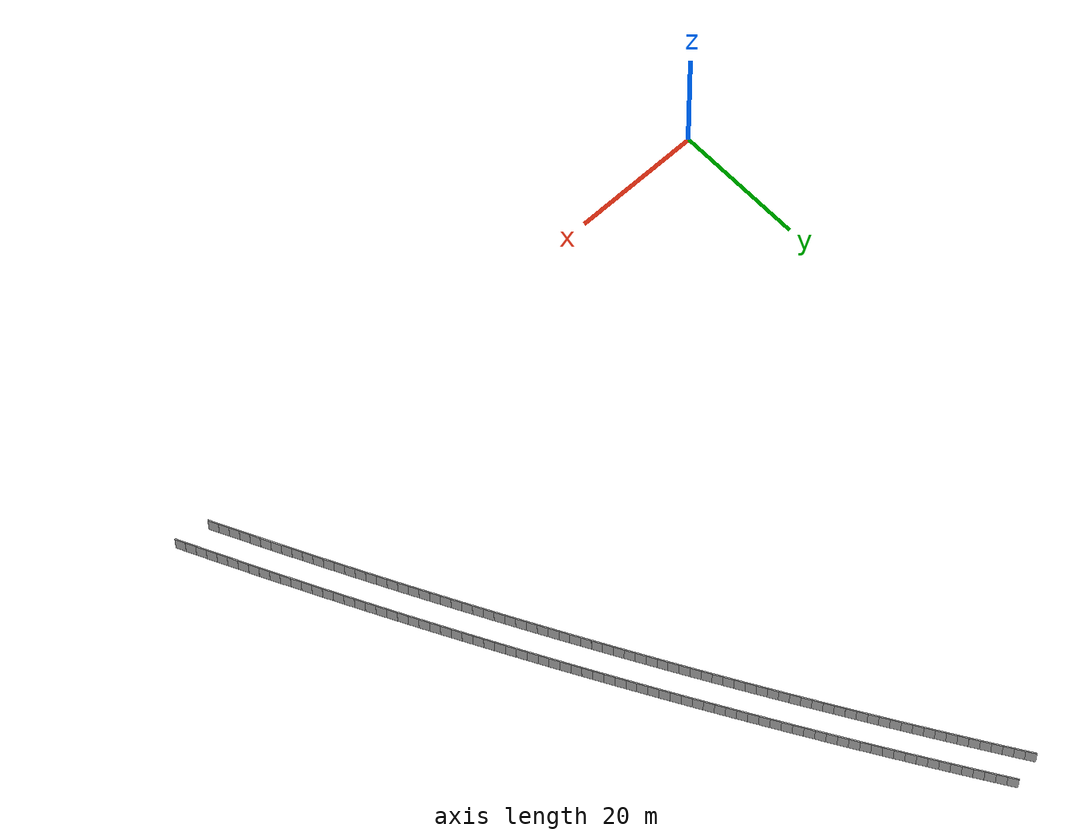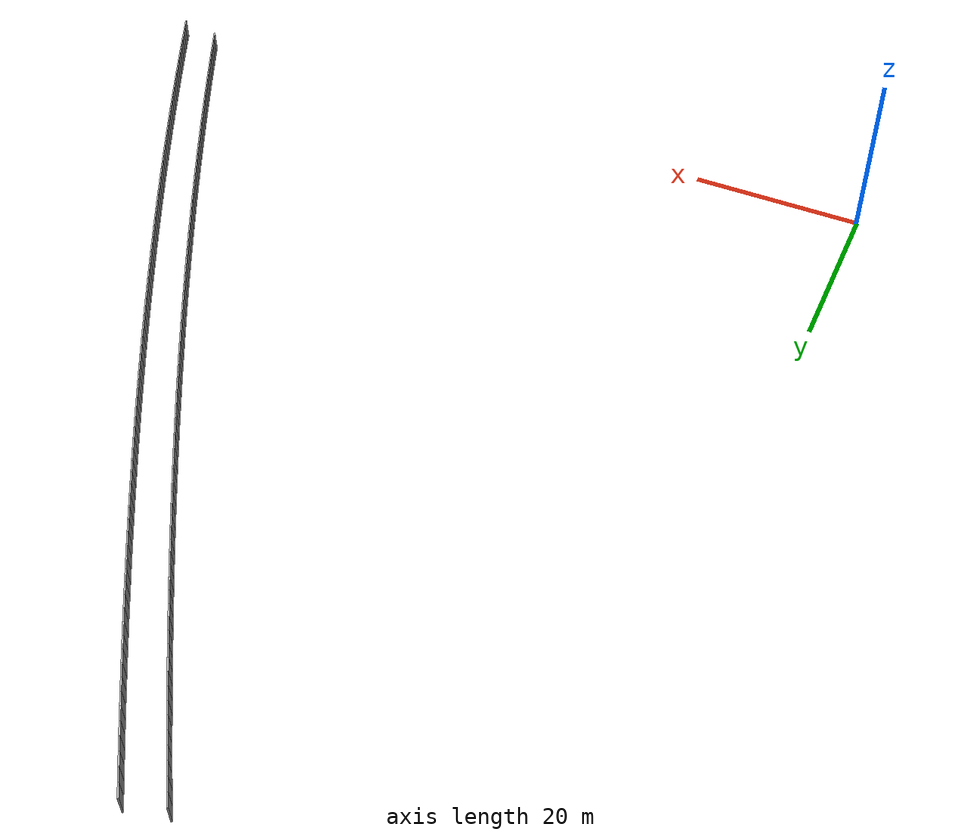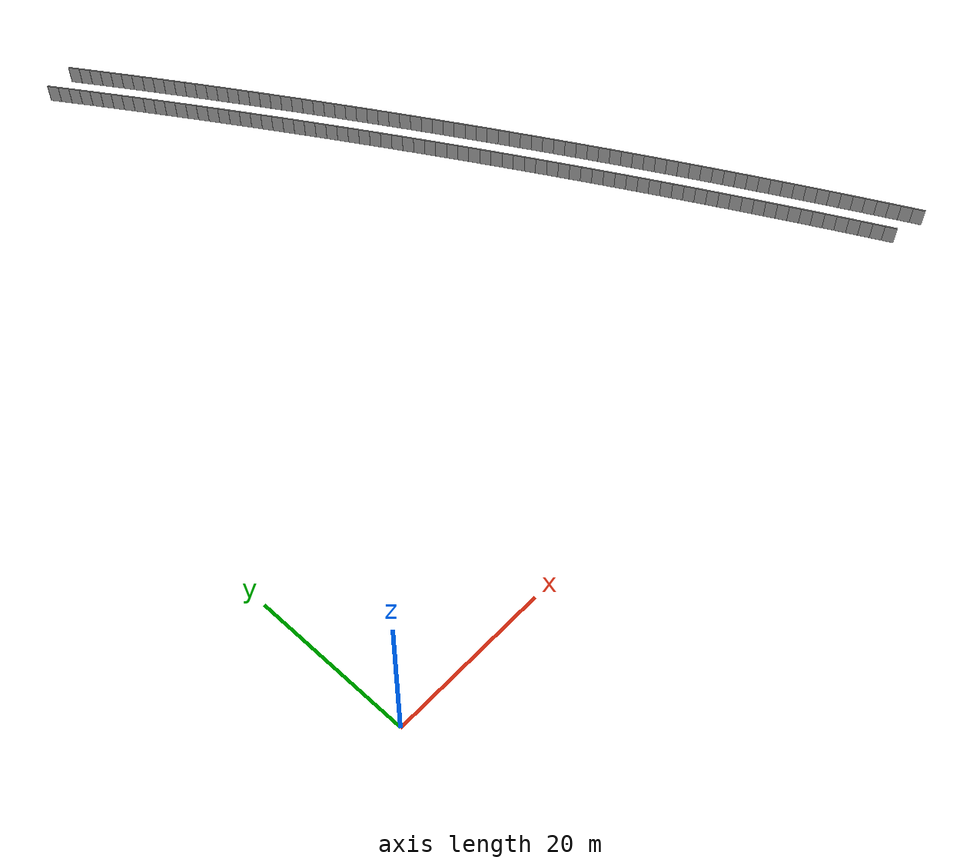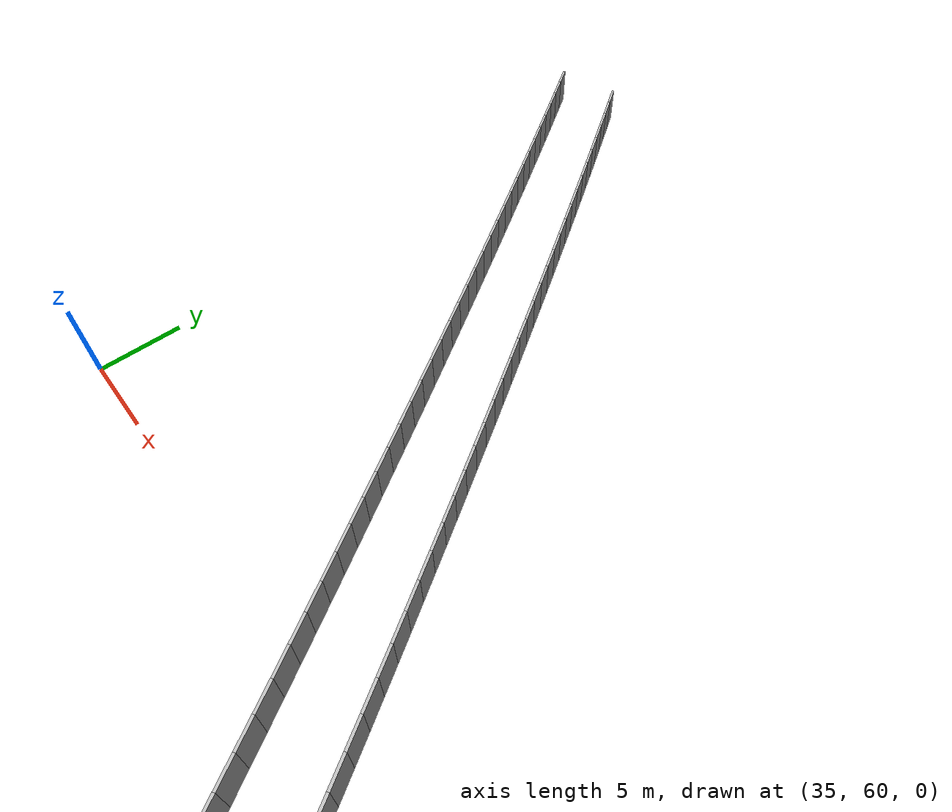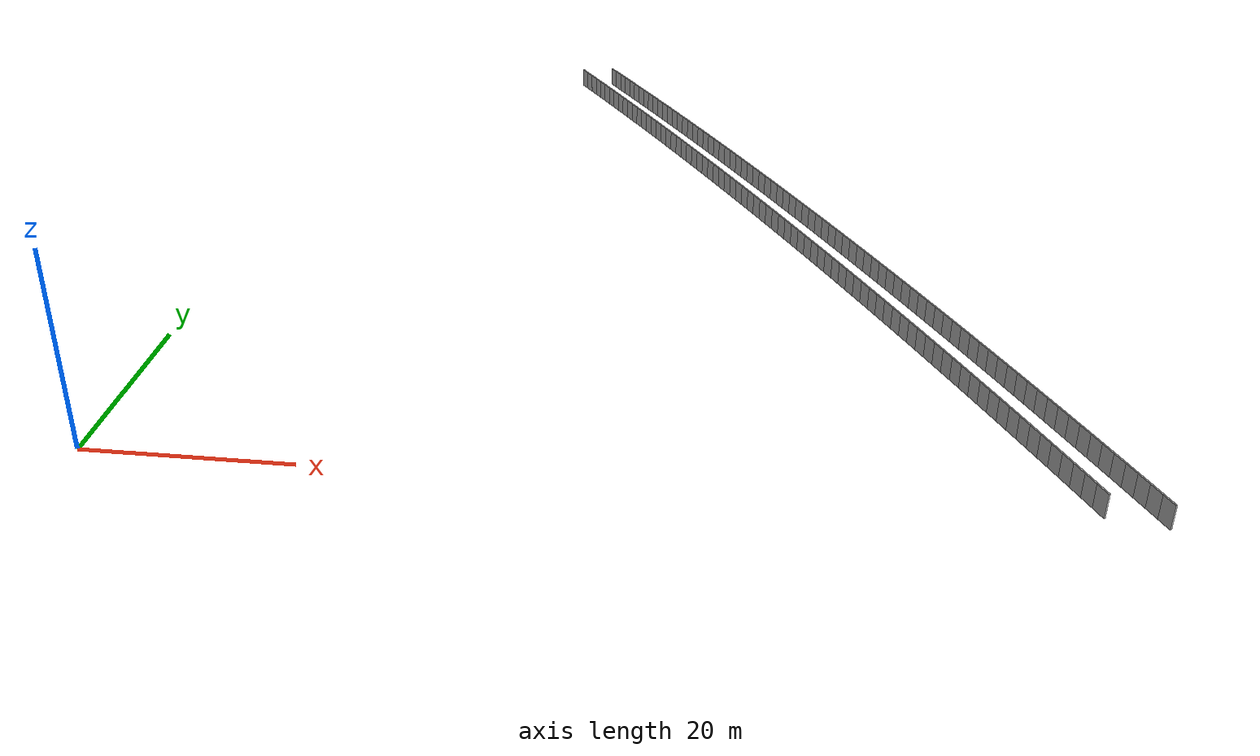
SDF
<?xml version="1.0" ?>
<sdf version="1.6">
  <model name="sps_2118">
    <pose frame="">0 0 0 0 -0 0</pose>
    <static>1</static>
    <self_collide>0</self_collide>
    <allow_auto_disable>0</allow_auto_disable>
    <link name="Wall10249">
      <kinematic>0</kinematic>
      <gravity>1</gravity>
      <self_collide>0</self_collide>
      <collision name="collision">
        <geometry>
          <box>
            <size>1.49655 0.15 2.5</size>
          </box>
        </geometry>
        <pose frame="">0 0 0 0 -0 0</pose>
      </collision>
      <visual name="visual">
        <geometry>
          <box>
            <size>1.49655 0.15 2.5</size>
          </box>
        </geometry>
        <pose frame="">0 0 0 0 -0 0</pose>
        <cast_shadows>1</cast_shadows>
        <transparency>0.0</transparency>
      </visual>
      <pose frame="">88.3077 1.14909 1.25 0 -0 2.0256</pose>
    </link>
    <link name="Wall10250">
      <kinematic>0</kinematic>
      <gravity>1</gravity>
      <self_collide>0</self_collide>
      <collision name="collision">
        <geometry>
          <box>
            <size>1.49631 0.15 2.5</size>
          </box>
        </geometry>
        <pose frame="">0 0 0 0 -0 0</pose>
      </collision>
      <visual name="visual">
        <geometry>
          <box>
            <size>1.49631 0.15 2.5</size>
          </box>
        </geometry>
        <pose frame="">0 0 0 0 -0 0</pose>
        <cast_shadows>1</cast_shadows>
        <transparency>0.0</transparency>
      </visual>
      <pose frame="">87.6493 2.4929 1.25 0 -0 2.02713</pose>
    </link>
    <link name="Wall10251">
      <kinematic>0</kinematic>
      <gravity>1</gravity>
      <self_collide>0</self_collide>
      <collision name="collision">
        <geometry>
          <box>
            <size>1.4966 0.15 2.5</size>
          </box>
        </geometry>
        <pose frame="">0 0 0 0 -0 0</pose>
      </collision>
      <visual name="visual">
        <geometry>
          <box>
            <size>1.4966 0.15 2.5</size>
          </box>
        </geometry>
        <pose frame="">0 0 0 0 -0 0</pose>
        <cast_shadows>1</cast_shadows>
        <transparency>0.0</transparency>
      </visual>
      <pose frame="">86.9889 3.83571 1.25 0 -0 2.02872</pose>
    </link>
    <link name="Wall10252">
      <kinematic>0</kinematic>
      <gravity>1</gravity>
      <self_collide>0</self_collide>
      <collision name="collision">
        <geometry>
          <box>
            <size>1.49645 0.15 2.5</size>
          </box>
        </geometry>
        <pose frame="">0 0 0 0 -0 0</pose>
      </collision>
      <visual name="visual">
        <geometry>
          <box>
            <size>1.49645 0.15 2.5</size>
          </box>
        </geometry>
        <pose frame="">0 0 0 0 -0 0</pose>
        <cast_shadows>1</cast_shadows>
        <transparency>0.0</transparency>
      </visual>
      <pose frame="">86.3262 5.1775 1.25 0 -0 2.03036</pose>
    </link>
    <link name="Wall10253">
      <kinematic>0</kinematic>
      <gravity>1</gravity>
      <self_collide>0</self_collide>
      <collision name="collision">
        <geometry>
          <box>
            <size>1.49649 0.15 2.5</size>
          </box>
        </geometry>
        <pose frame="">0 0 0 0 -0 0</pose>
      </collision>
      <visual name="visual">
        <geometry>
          <box>
            <size>1.49649 0.15 2.5</size>
          </box>
        </geometry>
        <pose frame="">0 0 0 0 -0 0</pose>
        <cast_shadows>1</cast_shadows>
        <transparency>0.0</transparency>
      </visual>
      <pose frame="">85.6614 6.5182 1.25 0 -0 2.03189</pose>
    </link>
    <link name="Wall10254">
      <kinematic>0</kinematic>
      <gravity>1</gravity>
      <self_collide>0</self_collide>
      <collision name="collision">
        <geometry>
          <box>
            <size>1.49663 0.15 2.5</size>
          </box>
        </geometry>
        <pose frame="">0 0 0 0 -0 0</pose>
      </collision>
      <visual name="visual">
        <geometry>
          <box>
            <size>1.49663 0.15 2.5</size>
          </box>
        </geometry>
        <pose frame="">0 0 0 0 -0 0</pose>
        <cast_shadows>1</cast_shadows>
        <transparency>0.0</transparency>
      </visual>
      <pose frame="">84.9943 7.85789 1.25 0 -0 2.03362</pose>
    </link>
    <link name="Wall10255">
      <kinematic>0</kinematic>
      <gravity>1</gravity>
      <self_collide>0</self_collide>
      <collision name="collision">
        <geometry>
          <box>
            <size>1.49646 0.15 2.5</size>
          </box>
        </geometry>
        <pose frame="">0 0 0 0 -0 0</pose>
      </collision>
      <visual name="visual">
        <geometry>
          <box>
            <size>1.49646 0.15 2.5</size>
          </box>
        </geometry>
        <pose frame="">0 0 0 0 -0 0</pose>
        <cast_shadows>1</cast_shadows>
        <transparency>0.0</transparency>
      </visual>
      <pose frame="">84.3252 9.19649 1.25 0 -0 2.03514</pose>
    </link>
    <link name="Wall10256">
      <kinematic>0</kinematic>
      <gravity>1</gravity>
      <self_collide>0</self_collide>
      <collision name="collision">
        <geometry>
          <box>
            <size>1.49647 0.15 2.5</size>
          </box>
        </geometry>
        <pose frame="">0 0 0 0 -0 0</pose>
      </collision>
      <visual name="visual">
        <geometry>
          <box>
            <size>1.49647 0.15 2.5</size>
          </box>
        </geometry>
        <pose frame="">0 0 0 0 -0 0</pose>
        <cast_shadows>1</cast_shadows>
        <transparency>0.0</transparency>
      </visual>
      <pose frame="">83.654 10.534 1.25 0 -0 2.03669</pose>
    </link>
    <link name="Wall10257">
      <kinematic>0</kinematic>
      <gravity>1</gravity>
      <self_collide>0</self_collide>
      <collision name="collision">
        <geometry>
          <box>
            <size>1.49664 0.15 2.5</size>
          </box>
        </geometry>
        <pose frame="">0 0 0 0 -0 0</pose>
      </collision>
      <visual name="visual">
        <geometry>
          <box>
            <size>1.49664 0.15 2.5</size>
          </box>
        </geometry>
        <pose frame="">0 0 0 0 -0 0</pose>
        <cast_shadows>1</cast_shadows>
        <transparency>0.0</transparency>
      </visual>
      <pose frame="">82.9806 11.8705 1.25 0 -0 2.03837</pose>
    </link>
    <link name="Wall10258">
      <kinematic>0</kinematic>
      <gravity>1</gravity>
      <self_collide>0</self_collide>
      <collision name="collision">
        <geometry>
          <box>
            <size>1.49643 0.15 2.5</size>
          </box>
        </geometry>
        <pose frame="">0 0 0 0 -0 0</pose>
      </collision>
      <visual name="visual">
        <geometry>
          <box>
            <size>1.49643 0.15 2.5</size>
          </box>
        </geometry>
        <pose frame="">0 0 0 0 -0 0</pose>
        <cast_shadows>1</cast_shadows>
        <transparency>0.0</transparency>
      </visual>
      <pose frame="">82.3051 13.2059 1.25 0 -0 2.03981</pose>
    </link>
    <link name="Wall10259">
      <kinematic>0</kinematic>
      <gravity>1</gravity>
      <self_collide>0</self_collide>
      <collision name="collision">
        <geometry>
          <box>
            <size>1.49623 0.15 2.5</size>
          </box>
        </geometry>
        <pose frame="">0 0 0 0 -0 0</pose>
      </collision>
      <visual name="visual">
        <geometry>
          <box>
            <size>1.49623 0.15 2.5</size>
          </box>
        </geometry>
        <pose frame="">0 0 0 0 -0 0</pose>
        <cast_shadows>1</cast_shadows>
        <transparency>0.0</transparency>
      </visual>
      <pose frame="">81.6275 14.54 1.25 0 -0 2.0417</pose>
    </link>
    <link name="Wall10260">
      <kinematic>0</kinematic>
      <gravity>1</gravity>
      <self_collide>0</self_collide>
      <collision name="collision">
        <geometry>
          <box>
            <size>1.49663 0.15 2.5</size>
          </box>
        </geometry>
        <pose frame="">0 0 0 0 -0 0</pose>
      </collision>
      <visual name="visual">
        <geometry>
          <box>
            <size>1.49663 0.15 2.5</size>
          </box>
        </geometry>
        <pose frame="">0 0 0 0 -0 0</pose>
        <cast_shadows>1</cast_shadows>
        <transparency>0.0</transparency>
      </visual>
      <pose frame="">80.9477 15.8731 1.25 0 -0 2.04303</pose>
    </link>
    <link name="Wall10261">
      <kinematic>0</kinematic>
      <gravity>1</gravity>
      <self_collide>0</self_collide>
      <collision name="collision">
        <geometry>
          <box>
            <size>1.49654 0.15 2.5</size>
          </box>
        </geometry>
        <pose frame="">0 0 0 0 -0 0</pose>
      </collision>
      <visual name="visual">
        <geometry>
          <box>
            <size>1.49654 0.15 2.5</size>
          </box>
        </geometry>
        <pose frame="">0 0 0 0 -0 0</pose>
        <cast_shadows>1</cast_shadows>
        <transparency>0.0</transparency>
      </visual>
      <pose frame="">80.2658 17.2053 1.25 0 -0 2.04471</pose>
    </link>
    <link name="Wall10262">
      <kinematic>0</kinematic>
      <gravity>1</gravity>
      <self_collide>0</self_collide>
      <collision name="collision">
        <geometry>
          <box>
            <size>1.49646 0.15 2.5</size>
          </box>
        </geometry>
        <pose frame="">0 0 0 0 -0 0</pose>
      </collision>
      <visual name="visual">
        <geometry>
          <box>
            <size>1.49646 0.15 2.5</size>
          </box>
        </geometry>
        <pose frame="">0 0 0 0 -0 0</pose>
        <cast_shadows>1</cast_shadows>
        <transparency>0.0</transparency>
      </visual>
      <pose frame="">79.5819 18.5364 1.25 0 -0 2.04612</pose>
    </link>
    <link name="Wall10263">
      <kinematic>0</kinematic>
      <gravity>1</gravity>
      <self_collide>0</self_collide>
      <collision name="collision">
        <geometry>
          <box>
            <size>1.49652 0.15 2.5</size>
          </box>
        </geometry>
        <pose frame="">0 0 0 0 -0 0</pose>
      </collision>
      <visual name="visual">
        <geometry>
          <box>
            <size>1.49652 0.15 2.5</size>
          </box>
        </geometry>
        <pose frame="">0 0 0 0 -0 0</pose>
        <cast_shadows>1</cast_shadows>
        <transparency>0.0</transparency>
      </visual>
      <pose frame="">78.8959 19.8664 1.25 0 -0 2.04789</pose>
    </link>
    <link name="Wall10264">
      <kinematic>0</kinematic>
      <gravity>1</gravity>
      <self_collide>0</self_collide>
      <collision name="collision">
        <geometry>
          <box>
            <size>1.49649 0.15 2.5</size>
          </box>
        </geometry>
        <pose frame="">0 0 0 0 -0 0</pose>
      </collision>
      <visual name="visual">
        <geometry>
          <box>
            <size>1.49649 0.15 2.5</size>
          </box>
        </geometry>
        <pose frame="">0 0 0 0 -0 0</pose>
        <cast_shadows>1</cast_shadows>
        <transparency>0.0</transparency>
      </visual>
      <pose frame="">78.2078 21.1953 1.25 0 -0 2.04927</pose>
    </link>
    <link name="Wall10265">
      <kinematic>0</kinematic>
      <gravity>1</gravity>
      <self_collide>0</self_collide>
      <collision name="collision">
        <geometry>
          <box>
            <size>1.49667 0.15 2.5</size>
          </box>
        </geometry>
        <pose frame="">0 0 0 0 -0 0</pose>
      </collision>
      <visual name="visual">
        <geometry>
          <box>
            <size>1.49667 0.15 2.5</size>
          </box>
        </geometry>
        <pose frame="">0 0 0 0 -0 0</pose>
        <cast_shadows>1</cast_shadows>
        <transparency>0.0</transparency>
      </visual>
      <pose frame="">77.5175 22.5232 1.25 0 -0 2.051</pose>
    </link>
    <link name="Wall10266">
      <kinematic>0</kinematic>
      <gravity>1</gravity>
      <self_collide>0</self_collide>
      <collision name="collision">
        <geometry>
          <box>
            <size>1.4964 0.15 2.5</size>
          </box>
        </geometry>
        <pose frame="">0 0 0 0 -0 0</pose>
      </collision>
      <visual name="visual">
        <geometry>
          <box>
            <size>1.4964 0.15 2.5</size>
          </box>
        </geometry>
        <pose frame="">0 0 0 0 -0 0</pose>
        <cast_shadows>1</cast_shadows>
        <transparency>0.0</transparency>
      </visual>
      <pose frame="">76.8252 23.85 1.25 0 -0 2.05243</pose>
    </link>
    <link name="Wall10267">
      <kinematic>0</kinematic>
      <gravity>1</gravity>
      <self_collide>0</self_collide>
      <collision name="collision">
        <geometry>
          <box>
            <size>1.49651 0.15 2.5</size>
          </box>
        </geometry>
        <pose frame="">0 0 0 0 -0 0</pose>
      </collision>
      <visual name="visual">
        <geometry>
          <box>
            <size>1.49651 0.15 2.5</size>
          </box>
        </geometry>
        <pose frame="">0 0 0 0 -0 0</pose>
        <cast_shadows>1</cast_shadows>
        <transparency>0.0</transparency>
      </visual>
      <pose frame="">76.1309 25.1756 1.25 0 -0 2.05424</pose>
    </link>
    <link name="Wall10268">
      <kinematic>0</kinematic>
      <gravity>1</gravity>
      <self_collide>0</self_collide>
      <collision name="collision">
        <geometry>
          <box>
            <size>1.4965 0.15 2.5</size>
          </box>
        </geometry>
        <pose frame="">0 0 0 0 -0 0</pose>
      </collision>
      <visual name="visual">
        <geometry>
          <box>
            <size>1.4965 0.15 2.5</size>
          </box>
        </geometry>
        <pose frame="">0 0 0 0 -0 0</pose>
        <cast_shadows>1</cast_shadows>
        <transparency>0.0</transparency>
      </visual>
      <pose frame="">75.4343 26.5001 1.25 0 -0 2.05571</pose>
    </link>
    <link name="Wall10269">
      <kinematic>0</kinematic>
      <gravity>1</gravity>
      <self_collide>0</self_collide>
      <collision name="collision">
        <geometry>
          <box>
            <size>1.49653 0.15 2.5</size>
          </box>
        </geometry>
        <pose frame="">0 0 0 0 -0 0</pose>
      </collision>
      <visual name="visual">
        <geometry>
          <box>
            <size>1.49653 0.15 2.5</size>
          </box>
        </geometry>
        <pose frame="">0 0 0 0 -0 0</pose>
        <cast_shadows>1</cast_shadows>
        <transparency>0.0</transparency>
      </visual>
      <pose frame="">74.7356 27.8235 1.25 0 -0 2.05741</pose>
    </link>
    <link name="Wall10270">
      <kinematic>0</kinematic>
      <gravity>1</gravity>
      <self_collide>0</self_collide>
      <collision name="collision">
        <geometry>
          <box>
            <size>1.49658 0.15 2.5</size>
          </box>
        </geometry>
        <pose frame="">0 0 0 0 -0 0</pose>
      </collision>
      <visual name="visual">
        <geometry>
          <box>
            <size>1.49658 0.15 2.5</size>
          </box>
        </geometry>
        <pose frame="">0 0 0 0 -0 0</pose>
        <cast_shadows>1</cast_shadows>
        <transparency>0.0</transparency>
      </visual>
      <pose frame="">74.0348 29.1458 1.25 0 -0 2.05887</pose>
    </link>
    <link name="Wall10271">
      <kinematic>0</kinematic>
      <gravity>1</gravity>
      <self_collide>0</self_collide>
      <collision name="collision">
        <geometry>
          <box>
            <size>1.49661 0.15 2.5</size>
          </box>
        </geometry>
        <pose frame="">0 0 0 0 -0 0</pose>
      </collision>
      <visual name="visual">
        <geometry>
          <box>
            <size>1.49661 0.15 2.5</size>
          </box>
        </geometry>
        <pose frame="">0 0 0 0 -0 0</pose>
        <cast_shadows>1</cast_shadows>
        <transparency>0.0</transparency>
      </visual>
      <pose frame="">73.332 30.4671 1.25 0 -0 2.06038</pose>
    </link>
    <link name="Wall10272">
      <kinematic>0</kinematic>
      <gravity>1</gravity>
      <self_collide>0</self_collide>
      <collision name="collision">
        <geometry>
          <box>
            <size>1.49657 0.15 2.5</size>
          </box>
        </geometry>
        <pose frame="">0 0 0 0 -0 0</pose>
      </collision>
      <visual name="visual">
        <geometry>
          <box>
            <size>1.49657 0.15 2.5</size>
          </box>
        </geometry>
        <pose frame="">0 0 0 0 -0 0</pose>
        <cast_shadows>1</cast_shadows>
        <transparency>0.0</transparency>
      </visual>
      <pose frame="">72.6271 31.7873 1.25 0 -0 2.06206</pose>
    </link>
    <link name="Wall10273">
      <kinematic>0</kinematic>
      <gravity>1</gravity>
      <self_collide>0</self_collide>
      <collision name="collision">
        <geometry>
          <box>
            <size>1.49628 0.15 2.5</size>
          </box>
        </geometry>
        <pose frame="">0 0 0 0 -0 0</pose>
      </collision>
      <visual name="visual">
        <geometry>
          <box>
            <size>1.49628 0.15 2.5</size>
          </box>
        </geometry>
        <pose frame="">0 0 0 0 -0 0</pose>
        <cast_shadows>1</cast_shadows>
        <transparency>0.0</transparency>
      </visual>
      <pose frame="">71.9201 33.1062 1.25 0 -0 2.06369</pose>
    </link>
    <link name="Wall10274">
      <kinematic>0</kinematic>
      <gravity>1</gravity>
      <self_collide>0</self_collide>
      <collision name="collision">
        <geometry>
          <box>
            <size>1.49668 0.15 2.5</size>
          </box>
        </geometry>
        <pose frame="">0 0 0 0 -0 0</pose>
      </collision>
      <visual name="visual">
        <geometry>
          <box>
            <size>1.49668 0.15 2.5</size>
          </box>
        </geometry>
        <pose frame="">0 0 0 0 -0 0</pose>
        <cast_shadows>1</cast_shadows>
        <transparency>0.0</transparency>
      </visual>
      <pose frame="">71.211 34.424 1.25 0 -0 2.06522</pose>
    </link>
    <link name="Wall10275">
      <kinematic>0</kinematic>
      <gravity>1</gravity>
      <self_collide>0</self_collide>
      <collision name="collision">
        <geometry>
          <box>
            <size>1.49651 0.15 2.5</size>
          </box>
        </geometry>
        <pose frame="">0 0 0 0 -0 0</pose>
      </collision>
      <visual name="visual">
        <geometry>
          <box>
            <size>1.49651 0.15 2.5</size>
          </box>
        </geometry>
        <pose frame="">0 0 0 0 -0 0</pose>
        <cast_shadows>1</cast_shadows>
        <transparency>0.0</transparency>
      </visual>
      <pose frame="">70.4997 35.7408 1.25 0 -0 2.06681</pose>
    </link>
    <link name="Wall10276">
      <kinematic>0</kinematic>
      <gravity>1</gravity>
      <self_collide>0</self_collide>
      <collision name="collision">
        <geometry>
          <box>
            <size>1.49651 0.15 2.5</size>
          </box>
        </geometry>
        <pose frame="">0 0 0 0 -0 0</pose>
      </collision>
      <visual name="visual">
        <geometry>
          <box>
            <size>1.49651 0.15 2.5</size>
          </box>
        </geometry>
        <pose frame="">0 0 0 0 -0 0</pose>
        <cast_shadows>1</cast_shadows>
        <transparency>0.0</transparency>
      </visual>
      <pose frame="">69.7865 37.0564 1.25 0 -0 2.06843</pose>
    </link>
    <link name="Wall10277">
      <kinematic>0</kinematic>
      <gravity>1</gravity>
      <self_collide>0</self_collide>
      <collision name="collision">
        <geometry>
          <box>
            <size>1.49634 0.15 2.5</size>
          </box>
        </geometry>
        <pose frame="">0 0 0 0 -0 0</pose>
      </collision>
      <visual name="visual">
        <geometry>
          <box>
            <size>1.49634 0.15 2.5</size>
          </box>
        </geometry>
        <pose frame="">0 0 0 0 -0 0</pose>
        <cast_shadows>1</cast_shadows>
        <transparency>0.0</transparency>
      </visual>
      <pose frame="">69.0712 38.3708 1.25 0 -0 2.06993</pose>
    </link>
    <link name="Wall10278">
      <kinematic>0</kinematic>
      <gravity>1</gravity>
      <self_collide>0</self_collide>
      <collision name="collision">
        <geometry>
          <box>
            <size>1.49651 0.15 2.5</size>
          </box>
        </geometry>
        <pose frame="">0 0 0 0 -0 0</pose>
      </collision>
      <visual name="visual">
        <geometry>
          <box>
            <size>1.49651 0.15 2.5</size>
          </box>
        </geometry>
        <pose frame="">0 0 0 0 -0 0</pose>
        <cast_shadows>1</cast_shadows>
        <transparency>0.0</transparency>
      </visual>
      <pose frame="">68.3538 39.6841 1.25 0 -0 2.0715</pose>
    </link>
    <link name="Wall10279">
      <kinematic>0</kinematic>
      <gravity>1</gravity>
      <self_collide>0</self_collide>
      <collision name="collision">
        <geometry>
          <box>
            <size>1.49655 0.15 2.5</size>
          </box>
        </geometry>
        <pose frame="">0 0 0 0 -0 0</pose>
      </collision>
      <visual name="visual">
        <geometry>
          <box>
            <size>1.49655 0.15 2.5</size>
          </box>
        </geometry>
        <pose frame="">0 0 0 0 -0 0</pose>
        <cast_shadows>1</cast_shadows>
        <transparency>0.0</transparency>
      </visual>
      <pose frame="">67.6344 40.9963 1.25 0 -0 2.07316</pose>
    </link>
    <link name="Wall10280">
      <kinematic>0</kinematic>
      <gravity>1</gravity>
      <self_collide>0</self_collide>
      <collision name="collision">
        <geometry>
          <box>
            <size>1.49639 0.15 2.5</size>
          </box>
        </geometry>
        <pose frame="">0 0 0 0 -0 0</pose>
      </collision>
      <visual name="visual">
        <geometry>
          <box>
            <size>1.49639 0.15 2.5</size>
          </box>
        </geometry>
        <pose frame="">0 0 0 0 -0 0</pose>
        <cast_shadows>1</cast_shadows>
        <transparency>0.0</transparency>
      </visual>
      <pose frame="">66.9128 42.3073 1.25 0 -0 2.07475</pose>
    </link>
    <link name="Wall10281">
      <kinematic>0</kinematic>
      <gravity>1</gravity>
      <self_collide>0</self_collide>
      <collision name="collision">
        <geometry>
          <box>
            <size>1.49651 0.15 2.5</size>
          </box>
        </geometry>
        <pose frame="">0 0 0 0 -0 0</pose>
      </collision>
      <visual name="visual">
        <geometry>
          <box>
            <size>1.49651 0.15 2.5</size>
          </box>
        </geometry>
        <pose frame="">0 0 0 0 -0 0</pose>
        <cast_shadows>1</cast_shadows>
        <transparency>0.0</transparency>
      </visual>
      <pose frame="">66.1892 43.6172 1.25 0 -0 2.07624</pose>
    </link>
    <link name="Wall10282">
      <kinematic>0</kinematic>
      <gravity>1</gravity>
      <self_collide>0</self_collide>
      <collision name="collision">
        <geometry>
          <box>
            <size>1.49681 0.15 2.5</size>
          </box>
        </geometry>
        <pose frame="">0 0 0 0 -0 0</pose>
      </collision>
      <visual name="visual">
        <geometry>
          <box>
            <size>1.49681 0.15 2.5</size>
          </box>
        </geometry>
        <pose frame="">0 0 0 0 -0 0</pose>
        <cast_shadows>1</cast_shadows>
        <transparency>0.0</transparency>
      </visual>
      <pose frame="">65.4634 44.9261 1.25 0 -0 2.07795</pose>
    </link>
    <link name="Wall10283">
      <kinematic>0</kinematic>
      <gravity>1</gravity>
      <self_collide>0</self_collide>
      <collision name="collision">
        <geometry>
          <box>
            <size>1.49648 0.15 2.5</size>
          </box>
        </geometry>
        <pose frame="">0 0 0 0 -0 0</pose>
      </collision>
      <visual name="visual">
        <geometry>
          <box>
            <size>1.49648 0.15 2.5</size>
          </box>
        </geometry>
        <pose frame="">0 0 0 0 -0 0</pose>
        <cast_shadows>1</cast_shadows>
        <transparency>0.0</transparency>
      </visual>
      <pose frame="">64.7355 46.2338 1.25 0 -0 2.07948</pose>
    </link>
    <link name="Wall10284">
      <kinematic>0</kinematic>
      <gravity>1</gravity>
      <self_collide>0</self_collide>
      <collision name="collision">
        <geometry>
          <box>
            <size>1.49609 0.15 2.5</size>
          </box>
        </geometry>
        <pose frame="">0 0 0 0 -0 0</pose>
      </collision>
      <visual name="visual">
        <geometry>
          <box>
            <size>1.49609 0.15 2.5</size>
          </box>
        </geometry>
        <pose frame="">0 0 0 0 -0 0</pose>
        <cast_shadows>1</cast_shadows>
        <transparency>0.0</transparency>
      </visual>
      <pose frame="">64.0055 47.5399 1.25 0 -0 2.08144</pose>
    </link>
    <link name="Wall10285">
      <kinematic>0</kinematic>
      <gravity>1</gravity>
      <self_collide>0</self_collide>
      <collision name="collision">
        <geometry>
          <box>
            <size>1.49665 0.15 2.5</size>
          </box>
        </geometry>
        <pose frame="">0 0 0 0 -0 0</pose>
      </collision>
      <visual name="visual">
        <geometry>
          <box>
            <size>1.49665 0.15 2.5</size>
          </box>
        </geometry>
        <pose frame="">0 0 0 0 -0 0</pose>
        <cast_shadows>1</cast_shadows>
        <transparency>0.0</transparency>
      </visual>
      <pose frame="">63.2732 48.8449 1.25 0 -0 2.08277</pose>
    </link>
    <link name="Wall10286">
      <kinematic>0</kinematic>
      <gravity>1</gravity>
      <self_collide>0</self_collide>
      <collision name="collision">
        <geometry>
          <box>
            <size>1.49635 0.15 2.5</size>
          </box>
        </geometry>
        <pose frame="">0 0 0 0 -0 0</pose>
      </collision>
      <visual name="visual">
        <geometry>
          <box>
            <size>1.49635 0.15 2.5</size>
          </box>
        </geometry>
        <pose frame="">0 0 0 0 -0 0</pose>
        <cast_shadows>1</cast_shadows>
        <transparency>0.0</transparency>
      </visual>
      <pose frame="">62.5391 50.149 1.25 0 -0 2.08425</pose>
    </link>
    <link name="Wall10287">
      <kinematic>0</kinematic>
      <gravity>1</gravity>
      <self_collide>0</self_collide>
      <collision name="collision">
        <geometry>
          <box>
            <size>1.49658 0.15 2.5</size>
          </box>
        </geometry>
        <pose frame="">0 0 0 0 -0 0</pose>
      </collision>
      <visual name="visual">
        <geometry>
          <box>
            <size>1.49658 0.15 2.5</size>
          </box>
        </geometry>
        <pose frame="">0 0 0 0 -0 0</pose>
        <cast_shadows>1</cast_shadows>
        <transparency>0.0</transparency>
      </visual>
      <pose frame="">61.8031 51.4519 1.25 0 -0 2.08585</pose>
    </link>
    <link name="Wall10288">
      <kinematic>0</kinematic>
      <gravity>1</gravity>
      <self_collide>0</self_collide>
      <collision name="collision">
        <geometry>
          <box>
            <size>1.49642 0.15 2.5</size>
          </box>
        </geometry>
        <pose frame="">0 0 0 0 -0 0</pose>
      </collision>
      <visual name="visual">
        <geometry>
          <box>
            <size>1.49642 0.15 2.5</size>
          </box>
        </geometry>
        <pose frame="">0 0 0 0 -0 0</pose>
        <cast_shadows>1</cast_shadows>
        <transparency>0.0</transparency>
      </visual>
      <pose frame="">61.065 52.7537 1.25 0 -0 2.08731</pose>
    </link>
    <link name="Wall10289">
      <kinematic>0</kinematic>
      <gravity>1</gravity>
      <self_collide>0</self_collide>
      <collision name="collision">
        <geometry>
          <box>
            <size>1.49661 0.15 2.5</size>
          </box>
        </geometry>
        <pose frame="">0 0 0 0 -0 0</pose>
      </collision>
      <visual name="visual">
        <geometry>
          <box>
            <size>1.49661 0.15 2.5</size>
          </box>
        </geometry>
        <pose frame="">0 0 0 0 -0 0</pose>
        <cast_shadows>1</cast_shadows>
        <transparency>0.0</transparency>
      </visual>
      <pose frame="">60.3249 54.0544 1.25 0 -0 2.08893</pose>
    </link>
    <link name="Wall10290">
      <kinematic>0</kinematic>
      <gravity>1</gravity>
      <self_collide>0</self_collide>
      <collision name="collision">
        <geometry>
          <box>
            <size>1.49653 0.15 2.5</size>
          </box>
        </geometry>
        <pose frame="">0 0 0 0 -0 0</pose>
      </collision>
      <visual name="visual">
        <geometry>
          <box>
            <size>1.49653 0.15 2.5</size>
          </box>
        </geometry>
        <pose frame="">0 0 0 0 -0 0</pose>
        <cast_shadows>1</cast_shadows>
        <transparency>0.0</transparency>
      </visual>
      <pose frame="">59.5825 55.3539 1.25 0 -0 2.09065</pose>
    </link>
    <link name="Wall10291">
      <kinematic>0</kinematic>
      <gravity>1</gravity>
      <self_collide>0</self_collide>
      <collision name="collision">
        <geometry>
          <box>
            <size>1.49635 0.15 2.5</size>
          </box>
        </geometry>
        <pose frame="">0 0 0 0 -0 0</pose>
      </collision>
      <visual name="visual">
        <geometry>
          <box>
            <size>1.49635 0.15 2.5</size>
          </box>
        </geometry>
        <pose frame="">0 0 0 0 -0 0</pose>
        <cast_shadows>1</cast_shadows>
        <transparency>0.0</transparency>
      </visual>
      <pose frame="">58.8382 56.6521 1.25 0 -0 2.09208</pose>
    </link>
    <link name="Wall10292">
      <kinematic>0</kinematic>
      <gravity>1</gravity>
      <self_collide>0</self_collide>
      <collision name="collision">
        <geometry>
          <box>
            <size>1.49667 0.15 2.5</size>
          </box>
        </geometry>
        <pose frame="">0 0 0 0 -0 0</pose>
      </collision>
      <visual name="visual">
        <geometry>
          <box>
            <size>1.49667 0.15 2.5</size>
          </box>
        </geometry>
        <pose frame="">0 0 0 0 -0 0</pose>
        <cast_shadows>1</cast_shadows>
        <transparency>0.0</transparency>
      </visual>
      <pose frame="">58.0918 57.9492 1.25 0 -0 2.09384</pose>
    </link>
    <link name="Wall10293">
      <kinematic>0</kinematic>
      <gravity>1</gravity>
      <self_collide>0</self_collide>
      <collision name="collision">
        <geometry>
          <box>
            <size>1.49639 0.15 2.5</size>
          </box>
        </geometry>
        <pose frame="">0 0 0 0 -0 0</pose>
      </collision>
      <visual name="visual">
        <geometry>
          <box>
            <size>1.49639 0.15 2.5</size>
          </box>
        </geometry>
        <pose frame="">0 0 0 0 -0 0</pose>
        <cast_shadows>1</cast_shadows>
        <transparency>0.0</transparency>
      </visual>
      <pose frame="">57.3433 59.2451 1.25 0 -0 2.09532</pose>
    </link>
    <link name="Wall10294">
      <kinematic>0</kinematic>
      <gravity>1</gravity>
      <self_collide>0</self_collide>
      <collision name="collision">
        <geometry>
          <box>
            <size>1.49651 0.15 2.5</size>
          </box>
        </geometry>
        <pose frame="">0 0 0 0 -0 0</pose>
      </collision>
      <visual name="visual">
        <geometry>
          <box>
            <size>1.49651 0.15 2.5</size>
          </box>
        </geometry>
        <pose frame="">0 0 0 0 -0 0</pose>
        <cast_shadows>1</cast_shadows>
        <transparency>0.0</transparency>
      </visual>
      <pose frame="">56.5929 60.5398 1.25 0 -0 2.09683</pose>
    </link>
    <link name="Wall10295">
      <kinematic>0</kinematic>
      <gravity>1</gravity>
      <self_collide>0</self_collide>
      <collision name="collision">
        <geometry>
          <box>
            <size>1.49656 0.15 2.5</size>
          </box>
        </geometry>
        <pose frame="">0 0 0 0 -0 0</pose>
      </collision>
      <visual name="visual">
        <geometry>
          <box>
            <size>1.49656 0.15 2.5</size>
          </box>
        </geometry>
        <pose frame="">0 0 0 0 -0 0</pose>
        <cast_shadows>1</cast_shadows>
        <transparency>0.0</transparency>
      </visual>
      <pose frame="">55.8404 61.8334 1.25 0 -0 2.09851</pose>
    </link>
    <link name="Wall10296">
      <kinematic>0</kinematic>
      <gravity>1</gravity>
      <self_collide>0</self_collide>
      <collision name="collision">
        <geometry>
          <box>
            <size>1.49657 0.15 2.5</size>
          </box>
        </geometry>
        <pose frame="">0 0 0 0 -0 0</pose>
      </collision>
      <visual name="visual">
        <geometry>
          <box>
            <size>1.49657 0.15 2.5</size>
          </box>
        </geometry>
        <pose frame="">0 0 0 0 -0 0</pose>
        <cast_shadows>1</cast_shadows>
        <transparency>0.0</transparency>
      </visual>
      <pose frame="">55.0858 63.1258 1.25 0 -0 2.10006</pose>
    </link>
    <link name="Wall10297">
      <kinematic>0</kinematic>
      <gravity>1</gravity>
      <self_collide>0</self_collide>
      <collision name="collision">
        <geometry>
          <box>
            <size>1.49651 0.15 2.5</size>
          </box>
        </geometry>
        <pose frame="">0 0 0 0 -0 0</pose>
      </collision>
      <visual name="visual">
        <geometry>
          <box>
            <size>1.49651 0.15 2.5</size>
          </box>
        </geometry>
        <pose frame="">0 0 0 0 -0 0</pose>
        <cast_shadows>1</cast_shadows>
        <transparency>0.0</transparency>
      </visual>
      <pose frame="">54.3292 64.417 1.25 0 -0 2.1016</pose>
    </link>
    <link name="Wall10298">
      <kinematic>0</kinematic>
      <gravity>1</gravity>
      <self_collide>0</self_collide>
      <collision name="collision">
        <geometry>
          <box>
            <size>1.49649 0.15 2.5</size>
          </box>
        </geometry>
        <pose frame="">0 0 0 0 -0 0</pose>
      </collision>
      <visual name="visual">
        <geometry>
          <box>
            <size>1.49649 0.15 2.5</size>
          </box>
        </geometry>
        <pose frame="">0 0 0 0 -0 0</pose>
        <cast_shadows>1</cast_shadows>
        <transparency>0.0</transparency>
      </visual>
      <pose frame="">53.5705 65.7069 1.25 0 -0 2.10335</pose>
    </link>
    <link name="Wall10299">
      <kinematic>0</kinematic>
      <gravity>1</gravity>
      <self_collide>0</self_collide>
      <collision name="collision">
        <geometry>
          <box>
            <size>1.49629 0.15 2.5</size>
          </box>
        </geometry>
        <pose frame="">0 0 0 0 -0 0</pose>
      </collision>
      <visual name="visual">
        <geometry>
          <box>
            <size>1.49629 0.15 2.5</size>
          </box>
        </geometry>
        <pose frame="">0 0 0 0 -0 0</pose>
        <cast_shadows>1</cast_shadows>
        <transparency>0.0</transparency>
      </visual>
      <pose frame="">52.8098 66.9955 1.25 0 -0 2.10481</pose>
    </link>
    <link name="Wall10300">
      <kinematic>0</kinematic>
      <gravity>1</gravity>
      <self_collide>0</self_collide>
      <collision name="collision">
        <geometry>
          <box>
            <size>1.49657 0.15 2.5</size>
          </box>
        </geometry>
        <pose frame="">0 0 0 0 -0 0</pose>
      </collision>
      <visual name="visual">
        <geometry>
          <box>
            <size>1.49657 0.15 2.5</size>
          </box>
        </geometry>
        <pose frame="">0 0 0 0 -0 0</pose>
        <cast_shadows>1</cast_shadows>
        <transparency>0.0</transparency>
      </visual>
      <pose frame="">52.0471 68.283 1.25 0 -0 2.1064</pose>
    </link>
    <link name="Wall10301">
      <kinematic>0</kinematic>
      <gravity>1</gravity>
      <self_collide>0</self_collide>
      <collision name="collision">
        <geometry>
          <box>
            <size>1.49669 0.15 2.5</size>
          </box>
        </geometry>
        <pose frame="">0 0 0 0 -0 0</pose>
      </collision>
      <visual name="visual">
        <geometry>
          <box>
            <size>1.49669 0.15 2.5</size>
          </box>
        </geometry>
        <pose frame="">0 0 0 0 -0 0</pose>
        <cast_shadows>1</cast_shadows>
        <transparency>0.0</transparency>
      </visual>
      <pose frame="">51.2822 69.5694 1.25 0 -0 2.10806</pose>
    </link>
    <link name="Wall10302">
      <kinematic>0</kinematic>
      <gravity>1</gravity>
      <self_collide>0</self_collide>
      <collision name="collision">
        <geometry>
          <box>
            <size>1.49643 0.15 2.5</size>
          </box>
        </geometry>
        <pose frame="">0 0 0 0 -0 0</pose>
      </collision>
      <visual name="visual">
        <geometry>
          <box>
            <size>1.49643 0.15 2.5</size>
          </box>
        </geometry>
        <pose frame="">0 0 0 0 -0 0</pose>
        <cast_shadows>1</cast_shadows>
        <transparency>0.0</transparency>
      </visual>
      <pose frame="">50.5153 70.8545 1.25 0 -0 2.10959</pose>
    </link>
    <link name="Wall10303">
      <kinematic>0</kinematic>
      <gravity>1</gravity>
      <self_collide>0</self_collide>
      <collision name="collision">
        <geometry>
          <box>
            <size>1.49663 0.15 2.5</size>
          </box>
        </geometry>
        <pose frame="">0 0 0 0 -0 0</pose>
      </collision>
      <visual name="visual">
        <geometry>
          <box>
            <size>1.49663 0.15 2.5</size>
          </box>
        </geometry>
        <pose frame="">0 0 0 0 -0 0</pose>
        <cast_shadows>1</cast_shadows>
        <transparency>0.0</transparency>
      </visual>
      <pose frame="">49.7465 72.1384 1.25 0 -0 2.11117</pose>
    </link>
    <link name="Wall10304">
      <kinematic>0</kinematic>
      <gravity>1</gravity>
      <self_collide>0</self_collide>
      <collision name="collision">
        <geometry>
          <box>
            <size>1.4965 0.15 2.5</size>
          </box>
        </geometry>
        <pose frame="">0 0 0 0 -0 0</pose>
      </collision>
      <visual name="visual">
        <geometry>
          <box>
            <size>1.4965 0.15 2.5</size>
          </box>
        </geometry>
        <pose frame="">0 0 0 0 -0 0</pose>
        <cast_shadows>1</cast_shadows>
        <transparency>0.0</transparency>
      </visual>
      <pose frame="">48.9755 73.4211 1.25 0 -0 2.11285</pose>
    </link>
    <link name="Wall10305">
      <kinematic>0</kinematic>
      <gravity>1</gravity>
      <self_collide>0</self_collide>
      <collision name="collision">
        <geometry>
          <box>
            <size>1.49658 0.15 2.5</size>
          </box>
        </geometry>
        <pose frame="">0 0 0 0 -0 0</pose>
      </collision>
      <visual name="visual">
        <geometry>
          <box>
            <size>1.49658 0.15 2.5</size>
          </box>
        </geometry>
        <pose frame="">0 0 0 0 -0 0</pose>
        <cast_shadows>1</cast_shadows>
        <transparency>0.0</transparency>
      </visual>
      <pose frame="">48.2025 74.7026 1.25 0 -0 2.1142</pose>
    </link>
    <link name="Wall10306">
      <kinematic>0</kinematic>
      <gravity>1</gravity>
      <self_collide>0</self_collide>
      <collision name="collision">
        <geometry>
          <box>
            <size>1.49636 0.15 2.5</size>
          </box>
        </geometry>
        <pose frame="">0 0 0 0 -0 0</pose>
      </collision>
      <visual name="visual">
        <geometry>
          <box>
            <size>1.49636 0.15 2.5</size>
          </box>
        </geometry>
        <pose frame="">0 0 0 0 -0 0</pose>
        <cast_shadows>1</cast_shadows>
        <transparency>0.0</transparency>
      </visual>
      <pose frame="">47.4276 75.9828 1.25 0 -0 2.116</pose>
    </link>
    <link name="Wall10307">
      <kinematic>0</kinematic>
      <gravity>1</gravity>
      <self_collide>0</self_collide>
      <collision name="collision">
        <geometry>
          <box>
            <size>1.49649 0.15 2.5</size>
          </box>
        </geometry>
        <pose frame="">0 0 0 0 -0 0</pose>
      </collision>
      <visual name="visual">
        <geometry>
          <box>
            <size>1.49649 0.15 2.5</size>
          </box>
        </geometry>
        <pose frame="">0 0 0 0 -0 0</pose>
        <cast_shadows>1</cast_shadows>
        <transparency>0.0</transparency>
      </visual>
      <pose frame="">46.6507 77.2617 1.25 0 -0 2.11748</pose>
    </link>
    <link name="Wall10308">
      <kinematic>0</kinematic>
      <gravity>1</gravity>
      <self_collide>0</self_collide>
      <collision name="collision">
        <geometry>
          <box>
            <size>1.49637 0.15 2.5</size>
          </box>
        </geometry>
        <pose frame="">0 0 0 0 -0 0</pose>
      </collision>
      <visual name="visual">
        <geometry>
          <box>
            <size>1.49637 0.15 2.5</size>
          </box>
        </geometry>
        <pose frame="">0 0 0 0 -0 0</pose>
        <cast_shadows>1</cast_shadows>
        <transparency>0.0</transparency>
      </visual>
      <pose frame="">45.8717 78.5394 1.25 0 -0 2.11915</pose>
    </link>
    <link name="Wall10309">
      <kinematic>0</kinematic>
      <gravity>1</gravity>
      <self_collide>0</self_collide>
      <collision name="collision">
        <geometry>
          <box>
            <size>1.49655 0.15 2.5</size>
          </box>
        </geometry>
        <pose frame="">0 0 0 0 -0 0</pose>
      </collision>
      <visual name="visual">
        <geometry>
          <box>
            <size>1.49655 0.15 2.5</size>
          </box>
        </geometry>
        <pose frame="">0 0 0 0 -0 0</pose>
        <cast_shadows>1</cast_shadows>
        <transparency>0.0</transparency>
      </visual>
      <pose frame="">45.0907 79.8159 1.25 0 -0 2.1206</pose>
    </link>
    <link name="Wall10310">
      <kinematic>0</kinematic>
      <gravity>1</gravity>
      <self_collide>0</self_collide>
      <collision name="collision">
        <geometry>
          <box>
            <size>1.49642 0.15 2.5</size>
          </box>
        </geometry>
        <pose frame="">0 0 0 0 -0 0</pose>
      </collision>
      <visual name="visual">
        <geometry>
          <box>
            <size>1.49642 0.15 2.5</size>
          </box>
        </geometry>
        <pose frame="">0 0 0 0 -0 0</pose>
        <cast_shadows>1</cast_shadows>
        <transparency>0.0</transparency>
      </visual>
      <pose frame="">44.3074 81.091 1.25 0 -0 2.12272</pose>
    </link>
    <link name="Wall10311">
      <kinematic>0</kinematic>
      <gravity>1</gravity>
      <self_collide>0</self_collide>
      <collision name="collision">
        <geometry>
          <box>
            <size>1.49643 0.15 2.5</size>
          </box>
        </geometry>
        <pose frame="">0 0 0 0 -0 0</pose>
      </collision>
      <visual name="visual">
        <geometry>
          <box>
            <size>1.49643 0.15 2.5</size>
          </box>
        </geometry>
        <pose frame="">0 0 0 0 -0 0</pose>
        <cast_shadows>1</cast_shadows>
        <transparency>0.0</transparency>
      </visual>
      <pose frame="">43.5221 82.3648 1.25 0 -0 2.12381</pose>
    </link>
    <link name="Wall10312">
      <kinematic>0</kinematic>
      <gravity>1</gravity>
      <self_collide>0</self_collide>
      <collision name="collision">
        <geometry>
          <box>
            <size>1.4966 0.15 2.5</size>
          </box>
        </geometry>
        <pose frame="">0 0 0 0 -0 0</pose>
      </collision>
      <visual name="visual">
        <geometry>
          <box>
            <size>1.4966 0.15 2.5</size>
          </box>
        </geometry>
        <pose frame="">0 0 0 0 -0 0</pose>
        <cast_shadows>1</cast_shadows>
        <transparency>0.0</transparency>
      </visual>
      <pose frame="">42.7349 83.6376 1.25 0 -0 2.12547</pose>
    </link>
    <link name="Wall10313">
      <kinematic>0</kinematic>
      <gravity>1</gravity>
      <self_collide>0</self_collide>
      <collision name="collision">
        <geometry>
          <box>
            <size>1.49634 0.15 2.5</size>
          </box>
        </geometry>
        <pose frame="">0 0 0 0 -0 0</pose>
      </collision>
      <visual name="visual">
        <geometry>
          <box>
            <size>1.49634 0.15 2.5</size>
          </box>
        </geometry>
        <pose frame="">0 0 0 0 -0 0</pose>
        <cast_shadows>1</cast_shadows>
        <transparency>0.0</transparency>
      </visual>
      <pose frame="">41.9459 84.9091 1.25 0 -0 2.12697</pose>
    </link>
    <link name="Wall10314">
      <kinematic>0</kinematic>
      <gravity>1</gravity>
      <self_collide>0</self_collide>
      <collision name="collision">
        <geometry>
          <box>
            <size>1.4965 0.15 2.5</size>
          </box>
        </geometry>
        <pose frame="">0 0 0 0 -0 0</pose>
      </collision>
      <visual name="visual">
        <geometry>
          <box>
            <size>1.4965 0.15 2.5</size>
          </box>
        </geometry>
        <pose frame="">0 0 0 0 -0 0</pose>
        <cast_shadows>1</cast_shadows>
        <transparency>0.0</transparency>
      </visual>
      <pose frame="">41.1547 86.1793 1.25 0 -0 2.12868</pose>
    </link>
    <link name="Wall10315">
      <kinematic>0</kinematic>
      <gravity>1</gravity>
      <self_collide>0</self_collide>
      <collision name="collision">
        <geometry>
          <box>
            <size>1.4965 0.15 2.5</size>
          </box>
        </geometry>
        <pose frame="">0 0 0 0 -0 0</pose>
      </collision>
      <visual name="visual">
        <geometry>
          <box>
            <size>1.4965 0.15 2.5</size>
          </box>
        </geometry>
        <pose frame="">0 0 0 0 -0 0</pose>
        <cast_shadows>1</cast_shadows>
        <transparency>0.0</transparency>
      </visual>
      <pose frame="">40.3615 87.4483 1.25 0 -0 2.13022</pose>
    </link>
    <link name="Wall10316">
      <kinematic>0</kinematic>
      <gravity>1</gravity>
      <self_collide>0</self_collide>
      <collision name="collision">
        <geometry>
          <box>
            <size>1.49658 0.15 2.5</size>
          </box>
        </geometry>
        <pose frame="">0 0 0 0 -0 0</pose>
      </collision>
      <visual name="visual">
        <geometry>
          <box>
            <size>1.49658 0.15 2.5</size>
          </box>
        </geometry>
        <pose frame="">0 0 0 0 -0 0</pose>
        <cast_shadows>1</cast_shadows>
        <transparency>0.0</transparency>
      </visual>
      <pose frame="">39.5663 88.7161 1.25 0 -0 2.13177</pose>
    </link>
    <link name="Wall10317">
      <kinematic>0</kinematic>
      <gravity>1</gravity>
      <self_collide>0</self_collide>
      <collision name="collision">
        <geometry>
          <box>
            <size>1.49659 0.15 2.5</size>
          </box>
        </geometry>
        <pose frame="">0 0 0 0 -0 0</pose>
      </collision>
      <visual name="visual">
        <geometry>
          <box>
            <size>1.49659 0.15 2.5</size>
          </box>
        </geometry>
        <pose frame="">0 0 0 0 -0 0</pose>
        <cast_shadows>1</cast_shadows>
        <transparency>0.0</transparency>
      </visual>
      <pose frame="">38.7692 89.9827 1.25 0 -0 2.13331</pose>
    </link>
    <link name="Wall10318">
      <kinematic>0</kinematic>
      <gravity>1</gravity>
      <self_collide>0</self_collide>
      <collision name="collision">
        <geometry>
          <box>
            <size>1.49642 0.15 2.5</size>
          </box>
        </geometry>
        <pose frame="">0 0 0 0 -0 0</pose>
      </collision>
      <visual name="visual">
        <geometry>
          <box>
            <size>1.49642 0.15 2.5</size>
          </box>
        </geometry>
        <pose frame="">0 0 0 0 -0 0</pose>
        <cast_shadows>1</cast_shadows>
        <transparency>0.0</transparency>
      </visual>
      <pose frame="">37.9701 91.248 1.25 0 -0 2.13488</pose>
    </link>
    <link name="Wall10319">
      <kinematic>0</kinematic>
      <gravity>1</gravity>
      <self_collide>0</self_collide>
      <collision name="collision">
        <geometry>
          <box>
            <size>1.49658 0.15 2.5</size>
          </box>
        </geometry>
        <pose frame="">0 0 0 0 -0 0</pose>
      </collision>
      <visual name="visual">
        <geometry>
          <box>
            <size>1.49658 0.15 2.5</size>
          </box>
        </geometry>
        <pose frame="">0 0 0 0 -0 0</pose>
        <cast_shadows>1</cast_shadows>
        <transparency>0.0</transparency>
      </visual>
      <pose frame="">37.1689 92.512 1.25 0 -0 2.1365</pose>
    </link>
    <link name="Wall10320">
      <kinematic>0</kinematic>
      <gravity>1</gravity>
      <self_collide>0</self_collide>
      <collision name="collision">
        <geometry>
          <box>
            <size>1.49648 0.15 2.5</size>
          </box>
        </geometry>
        <pose frame="">0 0 0 0 -0 0</pose>
      </collision>
      <visual name="visual">
        <geometry>
          <box>
            <size>1.49648 0.15 2.5</size>
          </box>
        </geometry>
        <pose frame="">0 0 0 0 -0 0</pose>
        <cast_shadows>1</cast_shadows>
        <transparency>0.0</transparency>
      </visual>
      <pose frame="">36.3657 93.7747 1.25 0 -0 2.13814</pose>
    </link>
    <link name="Wall10321">
      <kinematic>0</kinematic>
      <gravity>1</gravity>
      <self_collide>0</self_collide>
      <collision name="collision">
        <geometry>
          <box>
            <size>1.49653 0.15 2.5</size>
          </box>
        </geometry>
        <pose frame="">0 0 0 0 -0 0</pose>
      </collision>
      <visual name="visual">
        <geometry>
          <box>
            <size>1.49653 0.15 2.5</size>
          </box>
        </geometry>
        <pose frame="">0 0 0 0 -0 0</pose>
        <cast_shadows>1</cast_shadows>
        <transparency>0.0</transparency>
      </visual>
      <pose frame="">35.5605 95.0361 1.25 0 -0 2.13972</pose>
    </link>
    <link name="Wall10322">
      <kinematic>0</kinematic>
      <gravity>1</gravity>
      <self_collide>0</self_collide>
      <collision name="collision">
        <geometry>
          <box>
            <size>1.4964 0.15 2.5</size>
          </box>
        </geometry>
        <pose frame="">0 0 0 0 -0 0</pose>
      </collision>
      <visual name="visual">
        <geometry>
          <box>
            <size>1.4964 0.15 2.5</size>
          </box>
        </geometry>
        <pose frame="">0 0 0 0 -0 0</pose>
        <cast_shadows>1</cast_shadows>
        <transparency>0.0</transparency>
      </visual>
      <pose frame="">34.7533 96.2962 1.25 0 -0 2.14132</pose>
    </link>
    <link name="Wall10323">
      <kinematic>0</kinematic>
      <gravity>1</gravity>
      <self_collide>0</self_collide>
      <collision name="collision">
        <geometry>
          <box>
            <size>1.49662 0.15 2.5</size>
          </box>
        </geometry>
        <pose frame="">0 0 0 0 -0 0</pose>
      </collision>
      <visual name="visual">
        <geometry>
          <box>
            <size>1.49662 0.15 2.5</size>
          </box>
        </geometry>
        <pose frame="">0 0 0 0 -0 0</pose>
        <cast_shadows>1</cast_shadows>
        <transparency>0.0</transparency>
      </visual>
      <pose frame="">33.9442 97.5551 1.25 0 -0 2.14283</pose>
    </link>
    <link name="Wall10324">
      <kinematic>0</kinematic>
      <gravity>1</gravity>
      <self_collide>0</self_collide>
      <collision name="collision">
        <geometry>
          <box>
            <size>1.49646 0.15 2.5</size>
          </box>
        </geometry>
        <pose frame="">0 0 0 0 -0 0</pose>
      </collision>
      <visual name="visual">
        <geometry>
          <box>
            <size>1.49646 0.15 2.5</size>
          </box>
        </geometry>
        <pose frame="">0 0 0 0 -0 0</pose>
        <cast_shadows>1</cast_shadows>
        <transparency>0.0</transparency>
      </visual>
      <pose frame="">33.133 98.8127 1.25 0 -0 2.14455</pose>
    </link>
    <link name="Wall10844">
      <kinematic>0</kinematic>
      <gravity>1</gravity>
      <self_collide>0</self_collide>
      <collision name="collision">
        <geometry>
          <box>
            <size>1.50298 0.15 2.5</size>
          </box>
        </geometry>
        <pose frame="">0 0 0 0 -0 0</pose>
      </collision>
      <visual name="visual">
        <geometry>
          <box>
            <size>1.50298 0.15 2.5</size>
          </box>
        </geometry>
        <pose frame="">0 0 0 0 -0 0</pose>
        <cast_shadows>1</cast_shadows>
        <transparency>0.0</transparency>
      </visual>
      <pose frame="">93.3434 0.265578 1.25 0 -0 2.0226</pose>
    </link>
    <link name="Wall10845">
      <kinematic>0</kinematic>
      <gravity>1</gravity>
      <self_collide>0</self_collide>
      <collision name="collision">
        <geometry>
          <box>
            <size>1.50312 0.15 2.5</size>
          </box>
        </geometry>
        <pose frame="">0 0 0 0 -0 0</pose>
      </collision>
      <visual name="visual">
        <geometry>
          <box>
            <size>1.50312 0.15 2.5</size>
          </box>
        </geometry>
        <pose frame="">0 0 0 0 -0 0</pose>
        <cast_shadows>1</cast_shadows>
        <transparency>0.0</transparency>
      </visual>
      <pose frame="">92.6863 1.61738 1.25 0 -0 2.02391</pose>
    </link>
    <link name="Wall10846">
      <kinematic>0</kinematic>
      <gravity>1</gravity>
      <self_collide>0</self_collide>
      <collision name="collision">
        <geometry>
          <box>
            <size>1.50302 0.15 2.5</size>
          </box>
        </geometry>
        <pose frame="">0 0 0 0 -0 0</pose>
      </collision>
      <visual name="visual">
        <geometry>
          <box>
            <size>1.50302 0.15 2.5</size>
          </box>
        </geometry>
        <pose frame="">0 0 0 0 -0 0</pose>
        <cast_shadows>1</cast_shadows>
        <transparency>0.0</transparency>
      </visual>
      <pose frame="">92.0271 2.96818 1.25 0 -0 2.02571</pose>
    </link>
    <link name="Wall10847">
      <kinematic>0</kinematic>
      <gravity>1</gravity>
      <self_collide>0</self_collide>
      <collision name="collision">
        <geometry>
          <box>
            <size>1.50308 0.15 2.5</size>
          </box>
        </geometry>
        <pose frame="">0 0 0 0 -0 0</pose>
      </collision>
      <visual name="visual">
        <geometry>
          <box>
            <size>1.50308 0.15 2.5</size>
          </box>
        </geometry>
        <pose frame="">0 0 0 0 -0 0</pose>
        <cast_shadows>1</cast_shadows>
        <transparency>0.0</transparency>
      </visual>
      <pose frame="">91.3657 4.31789 1.25 0 -0 2.02718</pose>
    </link>
    <link name="Wall10848">
      <kinematic>0</kinematic>
      <gravity>1</gravity>
      <self_collide>0</self_collide>
      <collision name="collision">
        <geometry>
          <box>
            <size>1.50312 0.15 2.5</size>
          </box>
        </geometry>
        <pose frame="">0 0 0 0 -0 0</pose>
      </collision>
      <visual name="visual">
        <geometry>
          <box>
            <size>1.50312 0.15 2.5</size>
          </box>
        </geometry>
        <pose frame="">0 0 0 0 -0 0</pose>
        <cast_shadows>1</cast_shadows>
        <transparency>0.0</transparency>
      </visual>
      <pose frame="">90.7021 5.66661 1.25 0 -0 2.0288</pose>
    </link>
    <link name="Wall10849">
      <kinematic>0</kinematic>
      <gravity>1</gravity>
      <self_collide>0</self_collide>
      <collision name="collision">
        <geometry>
          <box>
            <size>1.50313 0.15 2.5</size>
          </box>
        </geometry>
        <pose frame="">0 0 0 0 -0 0</pose>
      </collision>
      <visual name="visual">
        <geometry>
          <box>
            <size>1.50313 0.15 2.5</size>
          </box>
        </geometry>
        <pose frame="">0 0 0 0 -0 0</pose>
        <cast_shadows>1</cast_shadows>
        <transparency>0.0</transparency>
      </visual>
      <pose frame="">90.0365 7.0143 1.25 0 -0 2.03038</pose>
    </link>
    <link name="Wall10850">
      <kinematic>0</kinematic>
      <gravity>1</gravity>
      <self_collide>0</self_collide>
      <collision name="collision">
        <geometry>
          <box>
            <size>1.50302 0.15 2.5</size>
          </box>
        </geometry>
        <pose frame="">0 0 0 0 -0 0</pose>
      </collision>
      <visual name="visual">
        <geometry>
          <box>
            <size>1.50302 0.15 2.5</size>
          </box>
        </geometry>
        <pose frame="">0 0 0 0 -0 0</pose>
        <cast_shadows>1</cast_shadows>
        <transparency>0.0</transparency>
      </visual>
      <pose frame="">89.3687 8.36088 1.25 0 -0 2.03196</pose>
    </link>
    <link name="Wall10851">
      <kinematic>0</kinematic>
      <gravity>1</gravity>
      <self_collide>0</self_collide>
      <collision name="collision">
        <geometry>
          <box>
            <size>1.5029 0.15 2.5</size>
          </box>
        </geometry>
        <pose frame="">0 0 0 0 -0 0</pose>
      </collision>
      <visual name="visual">
        <geometry>
          <box>
            <size>1.5029 0.15 2.5</size>
          </box>
        </geometry>
        <pose frame="">0 0 0 0 -0 0</pose>
        <cast_shadows>1</cast_shadows>
        <transparency>0.0</transparency>
      </visual>
      <pose frame="">88.6988 9.70628 1.25 0 -0 2.03363</pose>
    </link>
    <link name="Wall10852">
      <kinematic>0</kinematic>
      <gravity>1</gravity>
      <self_collide>0</self_collide>
      <collision name="collision">
        <geometry>
          <box>
            <size>1.50315 0.15 2.5</size>
          </box>
        </geometry>
        <pose frame="">0 0 0 0 -0 0</pose>
      </collision>
      <visual name="visual">
        <geometry>
          <box>
            <size>1.50315 0.15 2.5</size>
          </box>
        </geometry>
        <pose frame="">0 0 0 0 -0 0</pose>
        <cast_shadows>1</cast_shadows>
        <transparency>0.0</transparency>
      </visual>
      <pose frame="">88.0267 11.0507 1.25 0 -0 2.03513</pose>
    </link>
    <link name="Wall10853">
      <kinematic>0</kinematic>
      <gravity>1</gravity>
      <self_collide>0</self_collide>
      <collision name="collision">
        <geometry>
          <box>
            <size>1.50321 0.15 2.5</size>
          </box>
        </geometry>
        <pose frame="">0 0 0 0 -0 0</pose>
      </collision>
      <visual name="visual">
        <geometry>
          <box>
            <size>1.50321 0.15 2.5</size>
          </box>
        </geometry>
        <pose frame="">0 0 0 0 -0 0</pose>
        <cast_shadows>1</cast_shadows>
        <transparency>0.0</transparency>
      </visual>
      <pose frame="">87.3525 12.3942 1.25 0 -0 2.03666</pose>
    </link>
    <link name="Wall10854">
      <kinematic>0</kinematic>
      <gravity>1</gravity>
      <self_collide>0</self_collide>
      <collision name="collision">
        <geometry>
          <box>
            <size>1.50308 0.15 2.5</size>
          </box>
        </geometry>
        <pose frame="">0 0 0 0 -0 0</pose>
      </collision>
      <visual name="visual">
        <geometry>
          <box>
            <size>1.50308 0.15 2.5</size>
          </box>
        </geometry>
        <pose frame="">0 0 0 0 -0 0</pose>
        <cast_shadows>1</cast_shadows>
        <transparency>0.0</transparency>
      </visual>
      <pose frame="">86.6762 13.7366 1.25 0 -0 2.03829</pose>
    </link>
    <link name="Wall10855">
      <kinematic>0</kinematic>
      <gravity>1</gravity>
      <self_collide>0</self_collide>
      <collision name="collision">
        <geometry>
          <box>
            <size>1.50285 0.15 2.5</size>
          </box>
        </geometry>
        <pose frame="">0 0 0 0 -0 0</pose>
      </collision>
      <visual name="visual">
        <geometry>
          <box>
            <size>1.50285 0.15 2.5</size>
          </box>
        </geometry>
        <pose frame="">0 0 0 0 -0 0</pose>
        <cast_shadows>1</cast_shadows>
        <transparency>0.0</transparency>
      </visual>
      <pose frame="">85.9977 15.0777 1.25 0 -0 2.04006</pose>
    </link>
    <link name="Wall10856">
      <kinematic>0</kinematic>
      <gravity>1</gravity>
      <self_collide>0</self_collide>
      <collision name="collision">
        <geometry>
          <box>
            <size>1.50302 0.15 2.5</size>
          </box>
        </geometry>
        <pose frame="">0 0 0 0 -0 0</pose>
      </collision>
      <visual name="visual">
        <geometry>
          <box>
            <size>1.50302 0.15 2.5</size>
          </box>
        </geometry>
        <pose frame="">0 0 0 0 -0 0</pose>
        <cast_shadows>1</cast_shadows>
        <transparency>0.0</transparency>
      </visual>
      <pose frame="">85.3171 16.4177 1.25 0 -0 2.04145</pose>
    </link>
    <link name="Wall10857">
      <kinematic>0</kinematic>
      <gravity>1</gravity>
      <self_collide>0</self_collide>
      <collision name="collision">
        <geometry>
          <box>
            <size>1.50318 0.15 2.5</size>
          </box>
        </geometry>
        <pose frame="">0 0 0 0 -0 0</pose>
      </collision>
      <visual name="visual">
        <geometry>
          <box>
            <size>1.50318 0.15 2.5</size>
          </box>
        </geometry>
        <pose frame="">0 0 0 0 -0 0</pose>
        <cast_shadows>1</cast_shadows>
        <transparency>0.0</transparency>
      </visual>
      <pose frame="">84.6344 17.7568 1.25 0 -0 2.04309</pose>
    </link>
    <link name="Wall10858">
      <kinematic>0</kinematic>
      <gravity>1</gravity>
      <self_collide>0</self_collide>
      <collision name="collision">
        <geometry>
          <box>
            <size>1.50314 0.15 2.5</size>
          </box>
        </geometry>
        <pose frame="">0 0 0 0 -0 0</pose>
      </collision>
      <visual name="visual">
        <geometry>
          <box>
            <size>1.50314 0.15 2.5</size>
          </box>
        </geometry>
        <pose frame="">0 0 0 0 -0 0</pose>
        <cast_shadows>1</cast_shadows>
        <transparency>0.0</transparency>
      </visual>
      <pose frame="">83.9495 19.0949 1.25 0 -0 2.04456</pose>
    </link>
    <link name="Wall10859">
      <kinematic>0</kinematic>
      <gravity>1</gravity>
      <self_collide>0</self_collide>
      <collision name="collision">
        <geometry>
          <box>
            <size>1.5029 0.15 2.5</size>
          </box>
        </geometry>
        <pose frame="">0 0 0 0 -0 0</pose>
      </collision>
      <visual name="visual">
        <geometry>
          <box>
            <size>1.5029 0.15 2.5</size>
          </box>
        </geometry>
        <pose frame="">0 0 0 0 -0 0</pose>
        <cast_shadows>1</cast_shadows>
        <transparency>0.0</transparency>
      </visual>
      <pose frame="">83.2627 20.4318 1.25 0 -0 2.04629</pose>
    </link>
    <link name="Wall10860">
      <kinematic>0</kinematic>
      <gravity>1</gravity>
      <self_collide>0</self_collide>
      <collision name="collision">
        <geometry>
          <box>
            <size>1.50326 0.15 2.5</size>
          </box>
        </geometry>
        <pose frame="">0 0 0 0 -0 0</pose>
      </collision>
      <visual name="visual">
        <geometry>
          <box>
            <size>1.50326 0.15 2.5</size>
          </box>
        </geometry>
        <pose frame="">0 0 0 0 -0 0</pose>
        <cast_shadows>1</cast_shadows>
        <transparency>0.0</transparency>
      </visual>
      <pose frame="">82.5736 21.7676 1.25 0 -0 2.04781</pose>
    </link>
    <link name="Wall10861">
      <kinematic>0</kinematic>
      <gravity>1</gravity>
      <self_collide>0</self_collide>
      <collision name="collision">
        <geometry>
          <box>
            <size>1.50296 0.15 2.5</size>
          </box>
        </geometry>
        <pose frame="">0 0 0 0 -0 0</pose>
      </collision>
      <visual name="visual">
        <geometry>
          <box>
            <size>1.50296 0.15 2.5</size>
          </box>
        </geometry>
        <pose frame="">0 0 0 0 -0 0</pose>
        <cast_shadows>1</cast_shadows>
        <transparency>0.0</transparency>
      </visual>
      <pose frame="">81.8825 23.1024 1.25 0 -0 2.04928</pose>
    </link>
    <link name="Wall10862">
      <kinematic>0</kinematic>
      <gravity>1</gravity>
      <self_collide>0</self_collide>
      <collision name="collision">
        <geometry>
          <box>
            <size>1.50303 0.15 2.5</size>
          </box>
        </geometry>
        <pose frame="">0 0 0 0 -0 0</pose>
      </collision>
      <visual name="visual">
        <geometry>
          <box>
            <size>1.50303 0.15 2.5</size>
          </box>
        </geometry>
        <pose frame="">0 0 0 0 -0 0</pose>
        <cast_shadows>1</cast_shadows>
        <transparency>0.0</transparency>
      </visual>
      <pose frame="">81.1893 24.436 1.25 0 -0 2.05104</pose>
    </link>
    <link name="Wall10863">
      <kinematic>0</kinematic>
      <gravity>1</gravity>
      <self_collide>0</self_collide>
      <collision name="collision">
        <geometry>
          <box>
            <size>1.50288 0.15 2.5</size>
          </box>
        </geometry>
        <pose frame="">0 0 0 0 -0 0</pose>
      </collision>
      <visual name="visual">
        <geometry>
          <box>
            <size>1.50288 0.15 2.5</size>
          </box>
        </geometry>
        <pose frame="">0 0 0 0 -0 0</pose>
        <cast_shadows>1</cast_shadows>
        <transparency>0.0</transparency>
      </visual>
      <pose frame="">80.4939 25.7684 1.25 0 -0 2.05261</pose>
    </link>
    <link name="Wall10864">
      <kinematic>0</kinematic>
      <gravity>1</gravity>
      <self_collide>0</self_collide>
      <collision name="collision">
        <geometry>
          <box>
            <size>1.5032 0.15 2.5</size>
          </box>
        </geometry>
        <pose frame="">0 0 0 0 -0 0</pose>
      </collision>
      <visual name="visual">
        <geometry>
          <box>
            <size>1.5032 0.15 2.5</size>
          </box>
        </geometry>
        <pose frame="">0 0 0 0 -0 0</pose>
        <cast_shadows>1</cast_shadows>
        <transparency>0.0</transparency>
      </visual>
      <pose frame="">79.7963 27.0998 1.25 0 -0 2.05415</pose>
    </link>
    <link name="Wall10865">
      <kinematic>0</kinematic>
      <gravity>1</gravity>
      <self_collide>0</self_collide>
      <collision name="collision">
        <geometry>
          <box>
            <size>1.50308 0.15 2.5</size>
          </box>
        </geometry>
        <pose frame="">0 0 0 0 -0 0</pose>
      </collision>
      <visual name="visual">
        <geometry>
          <box>
            <size>1.50308 0.15 2.5</size>
          </box>
        </geometry>
        <pose frame="">0 0 0 0 -0 0</pose>
        <cast_shadows>1</cast_shadows>
        <transparency>0.0</transparency>
      </visual>
      <pose frame="">79.0968 28.4302 1.25 0 -0 2.05566</pose>
    </link>
    <link name="Wall10866">
      <kinematic>0</kinematic>
      <gravity>1</gravity>
      <self_collide>0</self_collide>
      <collision name="collision">
        <geometry>
          <box>
            <size>1.50313 0.15 2.5</size>
          </box>
        </geometry>
        <pose frame="">0 0 0 0 -0 0</pose>
      </collision>
      <visual name="visual">
        <geometry>
          <box>
            <size>1.50313 0.15 2.5</size>
          </box>
        </geometry>
        <pose frame="">0 0 0 0 -0 0</pose>
        <cast_shadows>1</cast_shadows>
        <transparency>0.0</transparency>
      </visual>
      <pose frame="">78.3952 29.7595 1.25 0 -0 2.0572</pose>
    </link>
    <link name="Wall10867">
      <kinematic>0</kinematic>
      <gravity>1</gravity>
      <self_collide>0</self_collide>
      <collision name="collision">
        <geometry>
          <box>
            <size>1.50317 0.15 2.5</size>
          </box>
        </geometry>
        <pose frame="">0 0 0 0 -0 0</pose>
      </collision>
      <visual name="visual">
        <geometry>
          <box>
            <size>1.50317 0.15 2.5</size>
          </box>
        </geometry>
        <pose frame="">0 0 0 0 -0 0</pose>
        <cast_shadows>1</cast_shadows>
        <transparency>0.0</transparency>
      </visual>
      <pose frame="">77.6913 31.0877 1.25 0 -0 2.05898</pose>
    </link>
    <link name="Wall10868">
      <kinematic>0</kinematic>
      <gravity>1</gravity>
      <self_collide>0</self_collide>
      <collision name="collision">
        <geometry>
          <box>
            <size>1.50297 0.15 2.5</size>
          </box>
        </geometry>
        <pose frame="">0 0 0 0 -0 0</pose>
      </collision>
      <visual name="visual">
        <geometry>
          <box>
            <size>1.50297 0.15 2.5</size>
          </box>
        </geometry>
        <pose frame="">0 0 0 0 -0 0</pose>
        <cast_shadows>1</cast_shadows>
        <transparency>0.0</transparency>
      </visual>
      <pose frame="">76.9854 32.4147 1.25 0 -0 2.06038</pose>
    </link>
    <link name="Wall10869">
      <kinematic>0</kinematic>
      <gravity>1</gravity>
      <self_collide>0</self_collide>
      <collision name="collision">
        <geometry>
          <box>
            <size>1.50318 0.15 2.5</size>
          </box>
        </geometry>
        <pose frame="">0 0 0 0 -0 0</pose>
      </collision>
      <visual name="visual">
        <geometry>
          <box>
            <size>1.50318 0.15 2.5</size>
          </box>
        </geometry>
        <pose frame="">0 0 0 0 -0 0</pose>
        <cast_shadows>1</cast_shadows>
        <transparency>0.0</transparency>
      </visual>
      <pose frame="">76.2775 33.7406 1.25 0 -0 2.0621</pose>
    </link>
    <link name="Wall10870">
      <kinematic>0</kinematic>
      <gravity>1</gravity>
      <self_collide>0</self_collide>
      <collision name="collision">
        <geometry>
          <box>
            <size>1.50314 0.15 2.5</size>
          </box>
        </geometry>
        <pose frame="">0 0 0 0 -0 0</pose>
      </collision>
      <visual name="visual">
        <geometry>
          <box>
            <size>1.50314 0.15 2.5</size>
          </box>
        </geometry>
        <pose frame="">0 0 0 0 -0 0</pose>
        <cast_shadows>1</cast_shadows>
        <transparency>0.0</transparency>
      </visual>
      <pose frame="">75.5673 35.0654 1.25 0 -0 2.06368</pose>
    </link>
    <link name="Wall10871">
      <kinematic>0</kinematic>
      <gravity>1</gravity>
      <self_collide>0</self_collide>
      <collision name="collision">
        <geometry>
          <box>
            <size>1.50299 0.15 2.5</size>
          </box>
        </geometry>
        <pose frame="">0 0 0 0 -0 0</pose>
      </collision>
      <visual name="visual">
        <geometry>
          <box>
            <size>1.50299 0.15 2.5</size>
          </box>
        </geometry>
        <pose frame="">0 0 0 0 -0 0</pose>
        <cast_shadows>1</cast_shadows>
        <transparency>0.0</transparency>
      </visual>
      <pose frame="">74.855 36.389 1.25 0 -0 2.06521</pose>
    </link>
    <link name="Wall10872">
      <kinematic>0</kinematic>
      <gravity>1</gravity>
      <self_collide>0</self_collide>
      <collision name="collision">
        <geometry>
          <box>
            <size>1.50317 0.15 2.5</size>
          </box>
        </geometry>
        <pose frame="">0 0 0 0 -0 0</pose>
      </collision>
      <visual name="visual">
        <geometry>
          <box>
            <size>1.50317 0.15 2.5</size>
          </box>
        </geometry>
        <pose frame="">0 0 0 0 -0 0</pose>
        <cast_shadows>1</cast_shadows>
        <transparency>0.0</transparency>
      </visual>
      <pose frame="">74.1407 37.7115 1.25 0 -0 2.06681</pose>
    </link>
    <link name="Wall10873">
      <kinematic>0</kinematic>
      <gravity>1</gravity>
      <self_collide>0</self_collide>
      <collision name="collision">
        <geometry>
          <box>
            <size>1.50306 0.15 2.5</size>
          </box>
        </geometry>
        <pose frame="">0 0 0 0 -0 0</pose>
      </collision>
      <visual name="visual">
        <geometry>
          <box>
            <size>1.50306 0.15 2.5</size>
          </box>
        </geometry>
        <pose frame="">0 0 0 0 -0 0</pose>
        <cast_shadows>1</cast_shadows>
        <transparency>0.0</transparency>
      </visual>
      <pose frame="">73.4243 39.0329 1.25 0 -0 2.06837</pose>
    </link>
    <link name="Wall10874">
      <kinematic>0</kinematic>
      <gravity>1</gravity>
      <self_collide>0</self_collide>
      <collision name="collision">
        <geometry>
          <box>
            <size>1.5032 0.15 2.5</size>
          </box>
        </geometry>
        <pose frame="">0 0 0 0 -0 0</pose>
      </collision>
      <visual name="visual">
        <geometry>
          <box>
            <size>1.5032 0.15 2.5</size>
          </box>
        </geometry>
        <pose frame="">0 0 0 0 -0 0</pose>
        <cast_shadows>1</cast_shadows>
        <transparency>0.0</transparency>
      </visual>
      <pose frame="">72.7058 40.3532 1.25 0 -0 2.06999</pose>
    </link>
    <link name="Wall10875">
      <kinematic>0</kinematic>
      <gravity>1</gravity>
      <self_collide>0</self_collide>
      <collision name="collision">
        <geometry>
          <box>
            <size>1.50296 0.15 2.5</size>
          </box>
        </geometry>
        <pose frame="">0 0 0 0 -0 0</pose>
      </collision>
      <visual name="visual">
        <geometry>
          <box>
            <size>1.50296 0.15 2.5</size>
          </box>
        </geometry>
        <pose frame="">0 0 0 0 -0 0</pose>
        <cast_shadows>1</cast_shadows>
        <transparency>0.0</transparency>
      </visual>
      <pose frame="">71.9853 41.6723 1.25 0 -0 2.07156</pose>
    </link>
    <link name="Wall10876">
      <kinematic>0</kinematic>
      <gravity>1</gravity>
      <self_collide>0</self_collide>
      <collision name="collision">
        <geometry>
          <box>
            <size>1.50304 0.15 2.5</size>
          </box>
        </geometry>
        <pose frame="">0 0 0 0 -0 0</pose>
      </collision>
      <visual name="visual">
        <geometry>
          <box>
            <size>1.50304 0.15 2.5</size>
          </box>
        </geometry>
        <pose frame="">0 0 0 0 -0 0</pose>
        <cast_shadows>1</cast_shadows>
        <transparency>0.0</transparency>
      </visual>
      <pose frame="">71.2627 42.9902 1.25 0 -0 2.0731</pose>
    </link>
    <link name="Wall10877">
      <kinematic>0</kinematic>
      <gravity>1</gravity>
      <self_collide>0</self_collide>
      <collision name="collision">
        <geometry>
          <box>
            <size>1.50306 0.15 2.5</size>
          </box>
        </geometry>
        <pose frame="">0 0 0 0 -0 0</pose>
      </collision>
      <visual name="visual">
        <geometry>
          <box>
            <size>1.50306 0.15 2.5</size>
          </box>
        </geometry>
        <pose frame="">0 0 0 0 -0 0</pose>
        <cast_shadows>1</cast_shadows>
        <transparency>0.0</transparency>
      </visual>
      <pose frame="">70.538 44.307 1.25 0 -0 2.07472</pose>
    </link>
    <link name="Wall10878">
      <kinematic>0</kinematic>
      <gravity>1</gravity>
      <self_collide>0</self_collide>
      <collision name="collision">
        <geometry>
          <box>
            <size>1.50308 0.15 2.5</size>
          </box>
        </geometry>
        <pose frame="">0 0 0 0 -0 0</pose>
      </collision>
      <visual name="visual">
        <geometry>
          <box>
            <size>1.50308 0.15 2.5</size>
          </box>
        </geometry>
        <pose frame="">0 0 0 0 -0 0</pose>
        <cast_shadows>1</cast_shadows>
        <transparency>0.0</transparency>
      </visual>
      <pose frame="">69.8111 45.6226 1.25 0 -0 2.07642</pose>
    </link>
    <link name="Wall10879">
      <kinematic>0</kinematic>
      <gravity>1</gravity>
      <self_collide>0</self_collide>
      <collision name="collision">
        <geometry>
          <box>
            <size>1.50287 0.15 2.5</size>
          </box>
        </geometry>
        <pose frame="">0 0 0 0 -0 0</pose>
      </collision>
      <visual name="visual">
        <geometry>
          <box>
            <size>1.50287 0.15 2.5</size>
          </box>
        </geometry>
        <pose frame="">0 0 0 0 -0 0</pose>
        <cast_shadows>1</cast_shadows>
        <transparency>0.0</transparency>
      </visual>
      <pose frame="">69.0821 46.937 1.25 0 -0 2.07785</pose>
    </link>
    <link name="Wall10880">
      <kinematic>0</kinematic>
      <gravity>1</gravity>
      <self_collide>0</self_collide>
      <collision name="collision">
        <geometry>
          <box>
            <size>1.50273 0.15 2.5</size>
          </box>
        </geometry>
        <pose frame="">0 0 0 0 -0 0</pose>
      </collision>
      <visual name="visual">
        <geometry>
          <box>
            <size>1.50273 0.15 2.5</size>
          </box>
        </geometry>
        <pose frame="">0 0 0 0 -0 0</pose>
        <cast_shadows>1</cast_shadows>
        <transparency>0.0</transparency>
      </visual>
      <pose frame="">68.3511 48.25 1.25 0 -0 2.07985</pose>
    </link>
    <link name="Wall10881">
      <kinematic>0</kinematic>
      <gravity>1</gravity>
      <self_collide>0</self_collide>
      <collision name="collision">
        <geometry>
          <box>
            <size>1.50312 0.15 2.5</size>
          </box>
        </geometry>
        <pose frame="">0 0 0 0 -0 0</pose>
      </collision>
      <visual name="visual">
        <geometry>
          <box>
            <size>1.50312 0.15 2.5</size>
          </box>
        </geometry>
        <pose frame="">0 0 0 0 -0 0</pose>
        <cast_shadows>1</cast_shadows>
        <transparency>0.0</transparency>
      </visual>
      <pose frame="">67.6178 49.5619 1.25 0 -0 2.08115</pose>
    </link>
    <link name="Wall10882">
      <kinematic>0</kinematic>
      <gravity>1</gravity>
      <self_collide>0</self_collide>
      <collision name="collision">
        <geometry>
          <box>
            <size>1.50323 0.15 2.5</size>
          </box>
        </geometry>
        <pose frame="">0 0 0 0 -0 0</pose>
      </collision>
      <visual name="visual">
        <geometry>
          <box>
            <size>1.50323 0.15 2.5</size>
          </box>
        </geometry>
        <pose frame="">0 0 0 0 -0 0</pose>
        <cast_shadows>1</cast_shadows>
        <transparency>0.0</transparency>
      </visual>
      <pose frame="">66.8825 50.873 1.25 0 -0 2.0826</pose>
    </link>
    <link name="Wall10883">
      <kinematic>0</kinematic>
      <gravity>1</gravity>
      <self_collide>0</self_collide>
      <collision name="collision">
        <geometry>
          <box>
            <size>1.50296 0.15 2.5</size>
          </box>
        </geometry>
        <pose frame="">0 0 0 0 -0 0</pose>
      </collision>
      <visual name="visual">
        <geometry>
          <box>
            <size>1.50296 0.15 2.5</size>
          </box>
        </geometry>
        <pose frame="">0 0 0 0 -0 0</pose>
        <cast_shadows>1</cast_shadows>
        <transparency>0.0</transparency>
      </visual>
      <pose frame="">66.1453 52.1829 1.25 0 -0 2.08419</pose>
    </link>
    <link name="Wall10884">
      <kinematic>0</kinematic>
      <gravity>1</gravity>
      <self_collide>0</self_collide>
      <collision name="collision">
        <geometry>
          <box>
            <size>1.50297 0.15 2.5</size>
          </box>
        </geometry>
        <pose frame="">0 0 0 0 -0 0</pose>
      </collision>
      <visual name="visual">
        <geometry>
          <box>
            <size>1.50297 0.15 2.5</size>
          </box>
        </geometry>
        <pose frame="">0 0 0 0 -0 0</pose>
        <cast_shadows>1</cast_shadows>
        <transparency>0.0</transparency>
      </visual>
      <pose frame="">65.4062 53.4915 1.25 0 -0 2.08577</pose>
    </link>
    <link name="Wall10885">
      <kinematic>0</kinematic>
      <gravity>1</gravity>
      <self_collide>0</self_collide>
      <collision name="collision">
        <geometry>
          <box>
            <size>1.50316 0.15 2.5</size>
          </box>
        </geometry>
        <pose frame="">0 0 0 0 -0 0</pose>
      </collision>
      <visual name="visual">
        <geometry>
          <box>
            <size>1.50316 0.15 2.5</size>
          </box>
        </geometry>
        <pose frame="">0 0 0 0 -0 0</pose>
        <cast_shadows>1</cast_shadows>
        <transparency>0.0</transparency>
      </visual>
      <pose frame="">64.6648 54.799 1.25 0 -0 2.08747</pose>
    </link>
    <link name="Wall10886">
      <kinematic>0</kinematic>
      <gravity>1</gravity>
      <self_collide>0</self_collide>
      <collision name="collision">
        <geometry>
          <box>
            <size>1.50314 0.15 2.5</size>
          </box>
        </geometry>
        <pose frame="">0 0 0 0 -0 0</pose>
      </collision>
      <visual name="visual">
        <geometry>
          <box>
            <size>1.50314 0.15 2.5</size>
          </box>
        </geometry>
        <pose frame="">0 0 0 0 -0 0</pose>
        <cast_shadows>1</cast_shadows>
        <transparency>0.0</transparency>
      </visual>
      <pose frame="">63.9213 56.1054 1.25 0 -0 2.08893</pose>
    </link>
    <link name="Wall10887">
      <kinematic>0</kinematic>
      <gravity>1</gravity>
      <self_collide>0</self_collide>
      <collision name="collision">
        <geometry>
          <box>
            <size>1.50309 0.15 2.5</size>
          </box>
        </geometry>
        <pose frame="">0 0 0 0 -0 0</pose>
      </collision>
      <visual name="visual">
        <geometry>
          <box>
            <size>1.50309 0.15 2.5</size>
          </box>
        </geometry>
        <pose frame="">0 0 0 0 -0 0</pose>
        <cast_shadows>1</cast_shadows>
        <transparency>0.0</transparency>
      </visual>
      <pose frame="">63.1757 57.4106 1.25 0 -0 2.09059</pose>
    </link>
    <link name="Wall10888">
      <kinematic>0</kinematic>
      <gravity>1</gravity>
      <self_collide>0</self_collide>
      <collision name="collision">
        <geometry>
          <box>
            <size>1.50308 0.15 2.5</size>
          </box>
        </geometry>
        <pose frame="">0 0 0 0 -0 0</pose>
      </collision>
      <visual name="visual">
        <geometry>
          <box>
            <size>1.50308 0.15 2.5</size>
          </box>
        </geometry>
        <pose frame="">0 0 0 0 -0 0</pose>
        <cast_shadows>1</cast_shadows>
        <transparency>0.0</transparency>
      </visual>
      <pose frame="">62.4282 58.7146 1.25 0 -0 2.09213</pose>
    </link>
    <link name="Wall10889">
      <kinematic>0</kinematic>
      <gravity>1</gravity>
      <self_collide>0</self_collide>
      <collision name="collision">
        <geometry>
          <box>
            <size>1.50303 0.15 2.5</size>
          </box>
        </geometry>
        <pose frame="">0 0 0 0 -0 0</pose>
      </collision>
      <visual name="visual">
        <geometry>
          <box>
            <size>1.50303 0.15 2.5</size>
          </box>
        </geometry>
        <pose frame="">0 0 0 0 -0 0</pose>
        <cast_shadows>1</cast_shadows>
        <transparency>0.0</transparency>
      </visual>
      <pose frame="">61.6786 60.0174 1.25 0 -0 2.0937</pose>
    </link>
    <link name="Wall10890">
      <kinematic>0</kinematic>
      <gravity>1</gravity>
      <self_collide>0</self_collide>
      <collision name="collision">
        <geometry>
          <box>
            <size>1.50297 0.15 2.5</size>
          </box>
        </geometry>
        <pose frame="">0 0 0 0 -0 0</pose>
      </collision>
      <visual name="visual">
        <geometry>
          <box>
            <size>1.50297 0.15 2.5</size>
          </box>
        </geometry>
        <pose frame="">0 0 0 0 -0 0</pose>
        <cast_shadows>1</cast_shadows>
        <transparency>0.0</transparency>
      </visual>
      <pose frame="">60.9268 61.3189 1.25 0 -0 2.09541</pose>
    </link>
    <link name="Wall10891">
      <kinematic>0</kinematic>
      <gravity>1</gravity>
      <self_collide>0</self_collide>
      <collision name="collision">
        <geometry>
          <box>
            <size>1.50305 0.15 2.5</size>
          </box>
        </geometry>
        <pose frame="">0 0 0 0 -0 0</pose>
      </collision>
      <visual name="visual">
        <geometry>
          <box>
            <size>1.50305 0.15 2.5</size>
          </box>
        </geometry>
        <pose frame="">0 0 0 0 -0 0</pose>
        <cast_shadows>1</cast_shadows>
        <transparency>0.0</transparency>
      </visual>
      <pose frame="">60.1731 62.6192 1.25 0 -0 2.09688</pose>
    </link>
    <link name="Wall10892">
      <kinematic>0</kinematic>
      <gravity>1</gravity>
      <self_collide>0</self_collide>
      <collision name="collision">
        <geometry>
          <box>
            <size>1.50304 0.15 2.5</size>
          </box>
        </geometry>
        <pose frame="">0 0 0 0 -0 0</pose>
      </collision>
      <visual name="visual">
        <geometry>
          <box>
            <size>1.50304 0.15 2.5</size>
          </box>
        </geometry>
        <pose frame="">0 0 0 0 -0 0</pose>
        <cast_shadows>1</cast_shadows>
        <transparency>0.0</transparency>
      </visual>
      <pose frame="">59.4173 63.9184 1.25 0 -0 2.09848</pose>
    </link>
    <link name="Wall10893">
      <kinematic>0</kinematic>
      <gravity>1</gravity>
      <self_collide>0</self_collide>
      <collision name="collision">
        <geometry>
          <box>
            <size>1.50306 0.15 2.5</size>
          </box>
        </geometry>
        <pose frame="">0 0 0 0 -0 0</pose>
      </collision>
      <visual name="visual">
        <geometry>
          <box>
            <size>1.50306 0.15 2.5</size>
          </box>
        </geometry>
        <pose frame="">0 0 0 0 -0 0</pose>
        <cast_shadows>1</cast_shadows>
        <transparency>0.0</transparency>
      </visual>
      <pose frame="">58.6594 65.2164 1.25 0 -0 2.10012</pose>
    </link>
    <link name="Wall10894">
      <kinematic>0</kinematic>
      <gravity>1</gravity>
      <self_collide>0</self_collide>
      <collision name="collision">
        <geometry>
          <box>
            <size>1.50308 0.15 2.5</size>
          </box>
        </geometry>
        <pose frame="">0 0 0 0 -0 0</pose>
      </collision>
      <visual name="visual">
        <geometry>
          <box>
            <size>1.50308 0.15 2.5</size>
          </box>
        </geometry>
        <pose frame="">0 0 0 0 -0 0</pose>
        <cast_shadows>1</cast_shadows>
        <transparency>0.0</transparency>
      </visual>
      <pose frame="">57.8994 66.5132 1.25 0 -0 2.10167</pose>
    </link>
    <link name="Wall10895">
      <kinematic>0</kinematic>
      <gravity>1</gravity>
      <self_collide>0</self_collide>
      <collision name="collision">
        <geometry>
          <box>
            <size>1.5031 0.15 2.5</size>
          </box>
        </geometry>
        <pose frame="">0 0 0 0 -0 0</pose>
      </collision>
      <visual name="visual">
        <geometry>
          <box>
            <size>1.5031 0.15 2.5</size>
          </box>
        </geometry>
        <pose frame="">0 0 0 0 -0 0</pose>
        <cast_shadows>1</cast_shadows>
        <transparency>0.0</transparency>
      </visual>
      <pose frame="">57.1374 67.8088 1.25 0 -0 2.10321</pose>
    </link>
    <link name="Wall10896">
      <kinematic>0</kinematic>
      <gravity>1</gravity>
      <self_collide>0</self_collide>
      <collision name="collision">
        <geometry>
          <box>
            <size>1.50311 0.15 2.5</size>
          </box>
        </geometry>
        <pose frame="">0 0 0 0 -0 0</pose>
      </collision>
      <visual name="visual">
        <geometry>
          <box>
            <size>1.50311 0.15 2.5</size>
          </box>
        </geometry>
        <pose frame="">0 0 0 0 -0 0</pose>
        <cast_shadows>1</cast_shadows>
        <transparency>0.0</transparency>
      </visual>
      <pose frame="">56.3733 69.1032 1.25 0 -0 2.10491</pose>
    </link>
    <link name="Wall10897">
      <kinematic>0</kinematic>
      <gravity>1</gravity>
      <self_collide>0</self_collide>
      <collision name="collision">
        <geometry>
          <box>
            <size>1.50305 0.15 2.5</size>
          </box>
        </geometry>
        <pose frame="">0 0 0 0 -0 0</pose>
      </collision>
      <visual name="visual">
        <geometry>
          <box>
            <size>1.50305 0.15 2.5</size>
          </box>
        </geometry>
        <pose frame="">0 0 0 0 -0 0</pose>
        <cast_shadows>1</cast_shadows>
        <transparency>0.0</transparency>
      </visual>
      <pose frame="">55.6072 70.3964 1.25 0 -0 2.10635</pose>
    </link>
    <link name="Wall10898">
      <kinematic>0</kinematic>
      <gravity>1</gravity>
      <self_collide>0</self_collide>
      <collision name="collision">
        <geometry>
          <box>
            <size>1.50296 0.15 2.5</size>
          </box>
        </geometry>
        <pose frame="">0 0 0 0 -0 0</pose>
      </collision>
      <visual name="visual">
        <geometry>
          <box>
            <size>1.50296 0.15 2.5</size>
          </box>
        </geometry>
        <pose frame="">0 0 0 0 -0 0</pose>
        <cast_shadows>1</cast_shadows>
        <transparency>0.0</transparency>
      </visual>
      <pose frame="">54.839 71.6883 1.25 0 -0 2.10808</pose>
    </link>
    <link name="Wall10899">
      <kinematic>0</kinematic>
      <gravity>1</gravity>
      <self_collide>0</self_collide>
      <collision name="collision">
        <geometry>
          <box>
            <size>1.50313 0.15 2.5</size>
          </box>
        </geometry>
        <pose frame="">0 0 0 0 -0 0</pose>
      </collision>
      <visual name="visual">
        <geometry>
          <box>
            <size>1.50313 0.15 2.5</size>
          </box>
        </geometry>
        <pose frame="">0 0 0 0 -0 0</pose>
        <cast_shadows>1</cast_shadows>
        <transparency>0.0</transparency>
      </visual>
      <pose frame="">54.0688 72.979 1.25 0 -0 2.10953</pose>
    </link>
    <link name="Wall10900">
      <kinematic>0</kinematic>
      <gravity>1</gravity>
      <self_collide>0</self_collide>
      <collision name="collision">
        <geometry>
          <box>
            <size>1.50321 0.15 2.5</size>
          </box>
        </geometry>
        <pose frame="">0 0 0 0 -0 0</pose>
      </collision>
      <visual name="visual">
        <geometry>
          <box>
            <size>1.50321 0.15 2.5</size>
          </box>
        </geometry>
        <pose frame="">0 0 0 0 -0 0</pose>
        <cast_shadows>1</cast_shadows>
        <transparency>0.0</transparency>
      </visual>
      <pose frame="">53.2966 74.2686 1.25 0 -0 2.1112</pose>
    </link>
    <link name="Wall10901">
      <kinematic>0</kinematic>
      <gravity>1</gravity>
      <self_collide>0</self_collide>
      <collision name="collision">
        <geometry>
          <box>
            <size>1.50311 0.15 2.5</size>
          </box>
        </geometry>
        <pose frame="">0 0 0 0 -0 0</pose>
      </collision>
      <visual name="visual">
        <geometry>
          <box>
            <size>1.50311 0.15 2.5</size>
          </box>
        </geometry>
        <pose frame="">0 0 0 0 -0 0</pose>
        <cast_shadows>1</cast_shadows>
        <transparency>0.0</transparency>
      </visual>
      <pose frame="">52.5223 75.557 1.25 0 -0 2.11266</pose>
    </link>
    <link name="Wall10902">
      <kinematic>0</kinematic>
      <gravity>1</gravity>
      <self_collide>0</self_collide>
      <collision name="collision">
        <geometry>
          <box>
            <size>1.50309 0.15 2.5</size>
          </box>
        </geometry>
        <pose frame="">0 0 0 0 -0 0</pose>
      </collision>
      <visual name="visual">
        <geometry>
          <box>
            <size>1.50309 0.15 2.5</size>
          </box>
        </geometry>
        <pose frame="">0 0 0 0 -0 0</pose>
        <cast_shadows>1</cast_shadows>
        <transparency>0.0</transparency>
      </visual>
      <pose frame="">51.746 76.8441 1.25 0 -0 2.11438</pose>
    </link>
    <link name="Wall10903">
      <kinematic>0</kinematic>
      <gravity>1</gravity>
      <self_collide>0</self_collide>
      <collision name="collision">
        <geometry>
          <box>
            <size>1.50304 0.15 2.5</size>
          </box>
        </geometry>
        <pose frame="">0 0 0 0 -0 0</pose>
      </collision>
      <visual name="visual">
        <geometry>
          <box>
            <size>1.50304 0.15 2.5</size>
          </box>
        </geometry>
        <pose frame="">0 0 0 0 -0 0</pose>
        <cast_shadows>1</cast_shadows>
        <transparency>0.0</transparency>
      </visual>
      <pose frame="">50.9676 78.1299 1.25 0 -0 2.11597</pose>
    </link>
    <link name="Wall10904">
      <kinematic>0</kinematic>
      <gravity>1</gravity>
      <self_collide>0</self_collide>
      <collision name="collision">
        <geometry>
          <box>
            <size>1.50306 0.15 2.5</size>
          </box>
        </geometry>
        <pose frame="">0 0 0 0 -0 0</pose>
      </collision>
      <visual name="visual">
        <geometry>
          <box>
            <size>1.50306 0.15 2.5</size>
          </box>
        </geometry>
        <pose frame="">0 0 0 0 -0 0</pose>
        <cast_shadows>1</cast_shadows>
        <transparency>0.0</transparency>
      </visual>
      <pose frame="">50.1872 79.4145 1.25 0 -0 2.11748</pose>
    </link>
    <link name="Wall10905">
      <kinematic>0</kinematic>
      <gravity>1</gravity>
      <self_collide>0</self_collide>
      <collision name="collision">
        <geometry>
          <box>
            <size>1.50266 0.15 2.5</size>
          </box>
        </geometry>
        <pose frame="">0 0 0 0 -0 0</pose>
      </collision>
      <visual name="visual">
        <geometry>
          <box>
            <size>1.50266 0.15 2.5</size>
          </box>
        </geometry>
        <pose frame="">0 0 0 0 -0 0</pose>
        <cast_shadows>1</cast_shadows>
        <transparency>0.0</transparency>
      </visual>
      <pose frame="">49.4046 80.6975 1.25 0 -0 2.11954</pose>
    </link>
    <link name="Wall10906">
      <kinematic>0</kinematic>
      <gravity>1</gravity>
      <self_collide>0</self_collide>
      <collision name="collision">
        <geometry>
          <box>
            <size>1.50302 0.15 2.5</size>
          </box>
        </geometry>
        <pose frame="">0 0 0 0 -0 0</pose>
      </collision>
      <visual name="visual">
        <geometry>
          <box>
            <size>1.50302 0.15 2.5</size>
          </box>
        </geometry>
        <pose frame="">0 0 0 0 -0 0</pose>
        <cast_shadows>1</cast_shadows>
        <transparency>0.0</transparency>
      </visual>
      <pose frame="">48.6199 81.9792 1.25 0 -0 2.12078</pose>
    </link>
    <link name="Wall10907">
      <kinematic>0</kinematic>
      <gravity>1</gravity>
      <self_collide>0</self_collide>
      <collision name="collision">
        <geometry>
          <box>
            <size>1.50314 0.15 2.5</size>
          </box>
        </geometry>
        <pose frame="">0 0 0 0 -0 0</pose>
      </collision>
      <visual name="visual">
        <geometry>
          <box>
            <size>1.50314 0.15 2.5</size>
          </box>
        </geometry>
        <pose frame="">0 0 0 0 -0 0</pose>
        <cast_shadows>1</cast_shadows>
        <transparency>0.0</transparency>
      </visual>
      <pose frame="">47.8334 83.2601 1.25 0 -0 2.12216</pose>
    </link>
    <link name="Wall10908">
      <kinematic>0</kinematic>
      <gravity>1</gravity>
      <self_collide>0</self_collide>
      <collision name="collision">
        <geometry>
          <box>
            <size>1.5031 0.15 2.5</size>
          </box>
        </geometry>
        <pose frame="">0 0 0 0 -0 0</pose>
      </collision>
      <visual name="visual">
        <geometry>
          <box>
            <size>1.5031 0.15 2.5</size>
          </box>
        </geometry>
        <pose frame="">0 0 0 0 -0 0</pose>
        <cast_shadows>1</cast_shadows>
        <transparency>0.0</transparency>
      </visual>
      <pose frame="">47.0449 84.5398 1.25 0 -0 2.12389</pose>
    </link>
    <link name="Wall10909">
      <kinematic>0</kinematic>
      <gravity>1</gravity>
      <self_collide>0</self_collide>
      <collision name="collision">
        <geometry>
          <box>
            <size>1.50314 0.15 2.5</size>
          </box>
        </geometry>
        <pose frame="">0 0 0 0 -0 0</pose>
      </collision>
      <visual name="visual">
        <geometry>
          <box>
            <size>1.50314 0.15 2.5</size>
          </box>
        </geometry>
        <pose frame="">0 0 0 0 -0 0</pose>
        <cast_shadows>1</cast_shadows>
        <transparency>0.0</transparency>
      </visual>
      <pose frame="">46.2543 85.8182 1.25 0 -0 2.1254</pose>
    </link>
    <link name="Wall10910">
      <kinematic>0</kinematic>
      <gravity>1</gravity>
      <self_collide>0</self_collide>
      <collision name="collision">
        <geometry>
          <box>
            <size>1.50299 0.15 2.5</size>
          </box>
        </geometry>
        <pose frame="">0 0 0 0 -0 0</pose>
      </collision>
      <visual name="visual">
        <geometry>
          <box>
            <size>1.50299 0.15 2.5</size>
          </box>
        </geometry>
        <pose frame="">0 0 0 0 -0 0</pose>
        <cast_shadows>1</cast_shadows>
        <transparency>0.0</transparency>
      </visual>
      <pose frame="">45.4617 87.0953 1.25 0 -0 2.12709</pose>
    </link>
    <link name="Wall10911">
      <kinematic>0</kinematic>
      <gravity>1</gravity>
      <self_collide>0</self_collide>
      <collision name="collision">
        <geometry>
          <box>
            <size>1.50304 0.15 2.5</size>
          </box>
        </geometry>
        <pose frame="">0 0 0 0 -0 0</pose>
      </collision>
      <visual name="visual">
        <geometry>
          <box>
            <size>1.50304 0.15 2.5</size>
          </box>
        </geometry>
        <pose frame="">0 0 0 0 -0 0</pose>
        <cast_shadows>1</cast_shadows>
        <transparency>0.0</transparency>
      </visual>
      <pose frame="">44.667 88.3711 1.25 0 -0 2.1286</pose>
    </link>
    <link name="Wall10912">
      <kinematic>0</kinematic>
      <gravity>1</gravity>
      <self_collide>0</self_collide>
      <collision name="collision">
        <geometry>
          <box>
            <size>1.50307 0.15 2.5</size>
          </box>
        </geometry>
        <pose frame="">0 0 0 0 -0 0</pose>
      </collision>
      <visual name="visual">
        <geometry>
          <box>
            <size>1.50307 0.15 2.5</size>
          </box>
        </geometry>
        <pose frame="">0 0 0 0 -0 0</pose>
        <cast_shadows>1</cast_shadows>
        <transparency>0.0</transparency>
      </visual>
      <pose frame="">43.8704 89.6457 1.25 0 -0 2.13017</pose>
    </link>
    <link name="Wall10913">
      <kinematic>0</kinematic>
      <gravity>1</gravity>
      <self_collide>0</self_collide>
      <collision name="collision">
        <geometry>
          <box>
            <size>1.50326 0.15 2.5</size>
          </box>
        </geometry>
        <pose frame="">0 0 0 0 -0 0</pose>
      </collision>
      <visual name="visual">
        <geometry>
          <box>
            <size>1.50326 0.15 2.5</size>
          </box>
        </geometry>
        <pose frame="">0 0 0 0 -0 0</pose>
        <cast_shadows>1</cast_shadows>
        <transparency>0.0</transparency>
      </visual>
      <pose frame="">43.0717 90.9191 1.25 0 -0 2.13181</pose>
    </link>
    <link name="Wall10914">
      <kinematic>0</kinematic>
      <gravity>1</gravity>
      <self_collide>0</self_collide>
      <collision name="collision">
        <geometry>
          <box>
            <size>1.50301 0.15 2.5</size>
          </box>
        </geometry>
        <pose frame="">0 0 0 0 -0 0</pose>
      </collision>
      <visual name="visual">
        <geometry>
          <box>
            <size>1.50301 0.15 2.5</size>
          </box>
        </geometry>
        <pose frame="">0 0 0 0 -0 0</pose>
        <cast_shadows>1</cast_shadows>
        <transparency>0.0</transparency>
      </visual>
      <pose frame="">42.271 92.1912 1.25 0 -0 2.13331</pose>
    </link>
    <link name="Wall10915">
      <kinematic>0</kinematic>
      <gravity>1</gravity>
      <self_collide>0</self_collide>
      <collision name="collision">
        <geometry>
          <box>
            <size>1.50305 0.15 2.5</size>
          </box>
        </geometry>
        <pose frame="">0 0 0 0 -0 0</pose>
      </collision>
      <visual name="visual">
        <geometry>
          <box>
            <size>1.50305 0.15 2.5</size>
          </box>
        </geometry>
        <pose frame="">0 0 0 0 -0 0</pose>
        <cast_shadows>1</cast_shadows>
        <transparency>0.0</transparency>
      </visual>
      <pose frame="">41.4685 93.462 1.25 0 -0 2.13488</pose>
    </link>
    <link name="Wall10916">
      <kinematic>0</kinematic>
      <gravity>1</gravity>
      <self_collide>0</self_collide>
      <collision name="collision">
        <geometry>
          <box>
            <size>1.50295 0.15 2.5</size>
          </box>
        </geometry>
        <pose frame="">0 0 0 0 -0 0</pose>
      </collision>
      <visual name="visual">
        <geometry>
          <box>
            <size>1.50295 0.15 2.5</size>
          </box>
        </geometry>
        <pose frame="">0 0 0 0 -0 0</pose>
        <cast_shadows>1</cast_shadows>
        <transparency>0.0</transparency>
      </visual>
      <pose frame="">40.6639 94.7315 1.25 0 -0 2.13651</pose>
    </link>
    <link name="Wall10917">
      <kinematic>0</kinematic>
      <gravity>1</gravity>
      <self_collide>0</self_collide>
      <collision name="collision">
        <geometry>
          <box>
            <size>1.5031 0.15 2.5</size>
          </box>
        </geometry>
        <pose frame="">0 0 0 0 -0 0</pose>
      </collision>
      <visual name="visual">
        <geometry>
          <box>
            <size>1.5031 0.15 2.5</size>
          </box>
        </geometry>
        <pose frame="">0 0 0 0 -0 0</pose>
        <cast_shadows>1</cast_shadows>
        <transparency>0.0</transparency>
      </visual>
      <pose frame="">39.8572 95.9997 1.25 0 -0 2.13818</pose>
    </link>
    <link name="Wall10918">
      <kinematic>0</kinematic>
      <gravity>1</gravity>
      <self_collide>0</self_collide>
      <collision name="collision">
        <geometry>
          <box>
            <size>1.5031 0.15 2.5</size>
          </box>
        </geometry>
        <pose frame="">0 0 0 0 -0 0</pose>
      </collision>
      <visual name="visual">
        <geometry>
          <box>
            <size>1.5031 0.15 2.5</size>
          </box>
        </geometry>
        <pose frame="">0 0 0 0 -0 0</pose>
        <cast_shadows>1</cast_shadows>
        <transparency>0.0</transparency>
      </visual>
      <pose frame="">39.0485 97.2667 1.25 0 -0 2.13962</pose>
    </link>
    <link name="Wall10919">
      <kinematic>0</kinematic>
      <gravity>1</gravity>
      <self_collide>0</self_collide>
      <collision name="collision">
        <geometry>
          <box>
            <size>1.50302 0.15 2.5</size>
          </box>
        </geometry>
        <pose frame="">0 0 0 0 -0 0</pose>
      </collision>
      <visual name="visual">
        <geometry>
          <box>
            <size>1.50302 0.15 2.5</size>
          </box>
        </geometry>
        <pose frame="">0 0 0 0 -0 0</pose>
        <cast_shadows>1</cast_shadows>
        <transparency>0.0</transparency>
      </visual>
      <pose frame="">38.2378 98.5324 1.25 0 -0 2.14134</pose>
    </link>
    <link name="Wall10920">
      <kinematic>0</kinematic>
      <gravity>1</gravity>
      <self_collide>0</self_collide>
      <collision name="collision">
        <geometry>
          <box>
            <size>1.50304 0.15 2.5</size>
          </box>
        </geometry>
        <pose frame="">0 0 0 0 -0 0</pose>
      </collision>
      <visual name="visual">
        <geometry>
          <box>
            <size>1.50304 0.15 2.5</size>
          </box>
        </geometry>
        <pose frame="">0 0 0 0 -0 0</pose>
        <cast_shadows>1</cast_shadows>
        <transparency>0.0</transparency>
      </visual>
      <pose frame="">37.4251 99.7968 1.25 0 -0 2.14278</pose>
    </link>
  </model>
</sdf>
